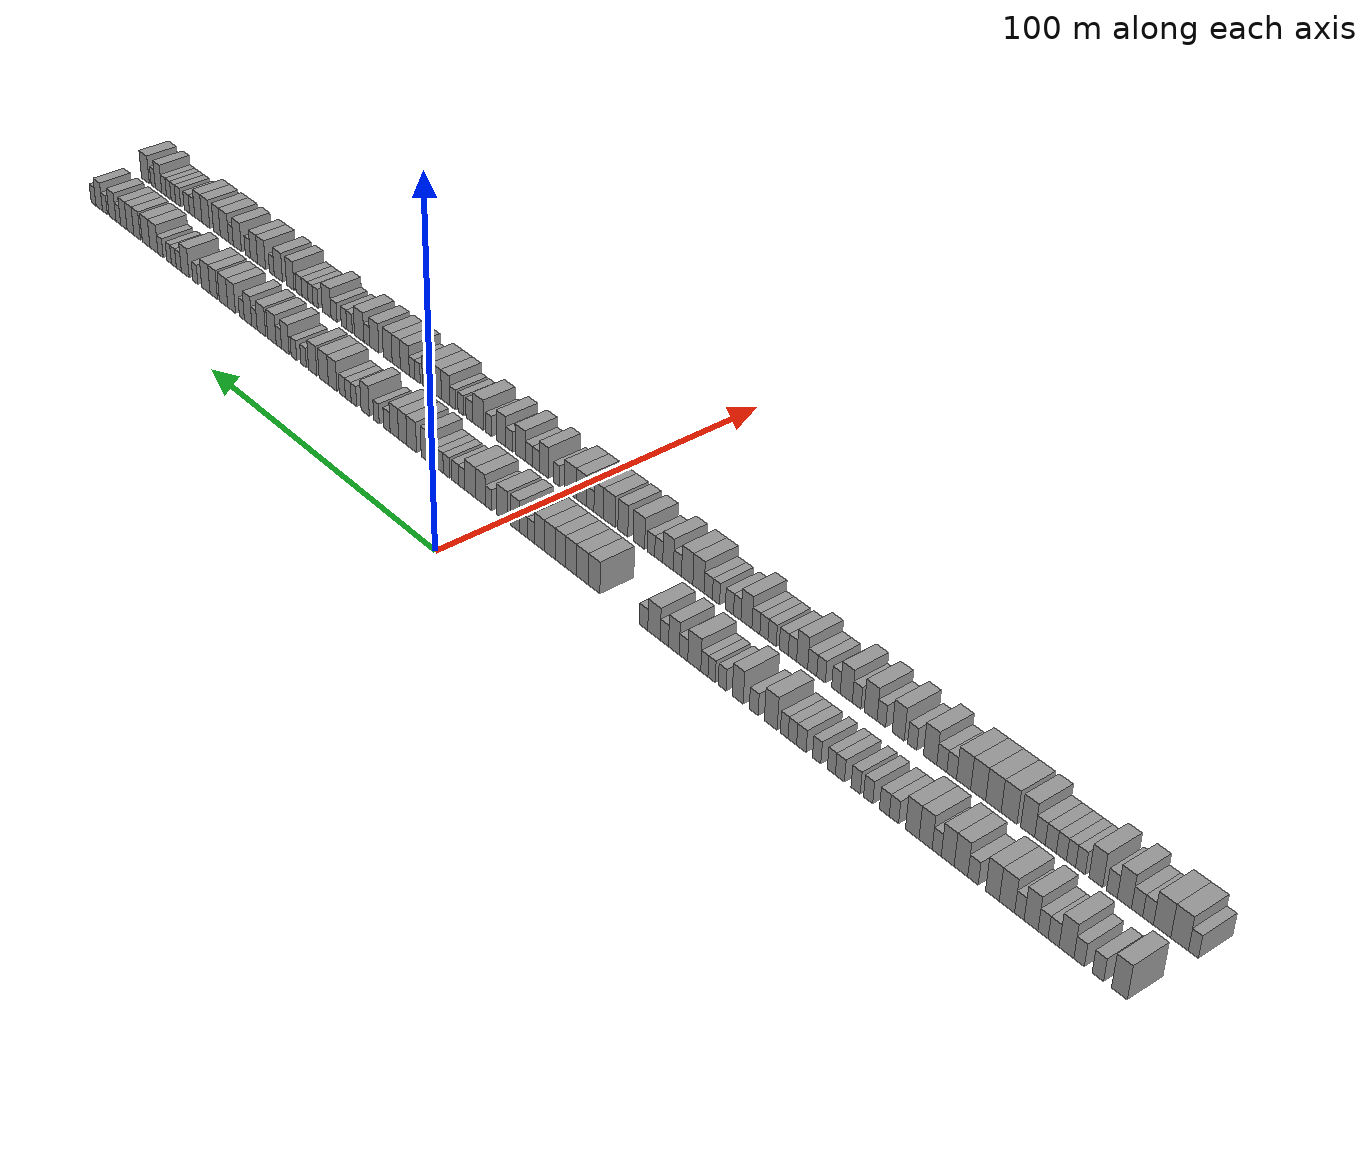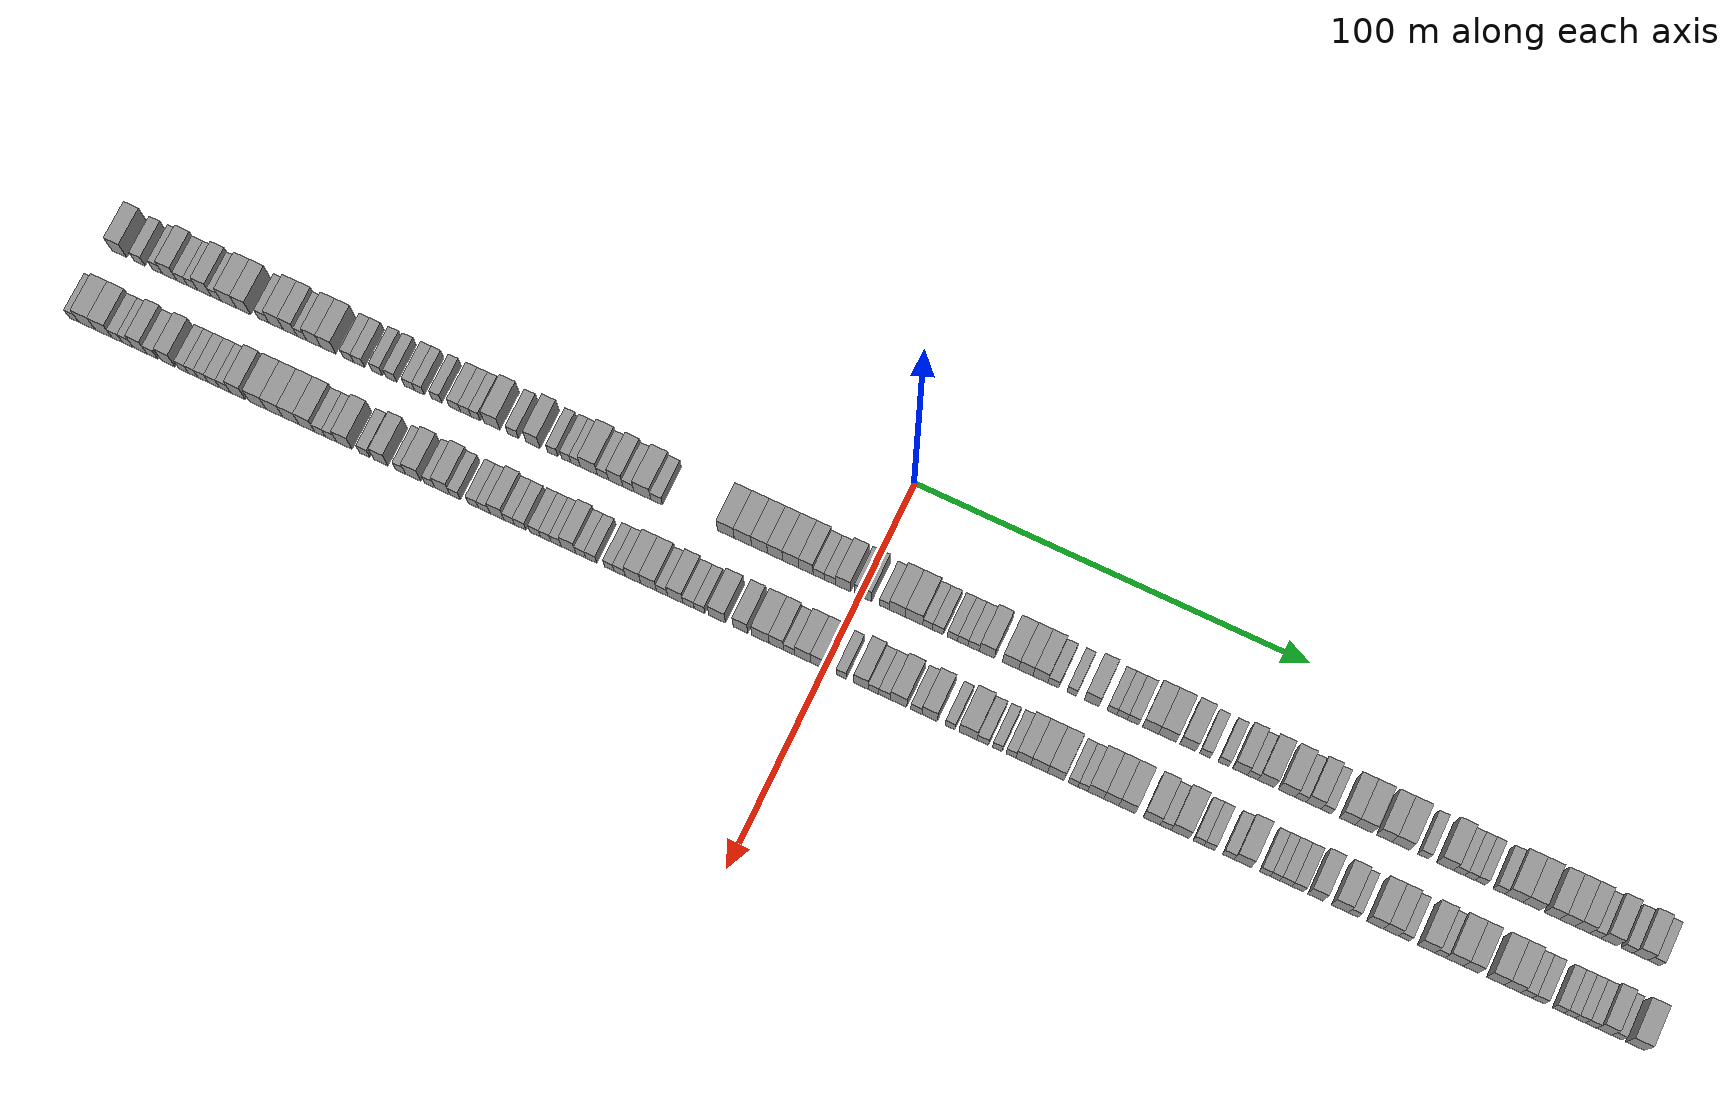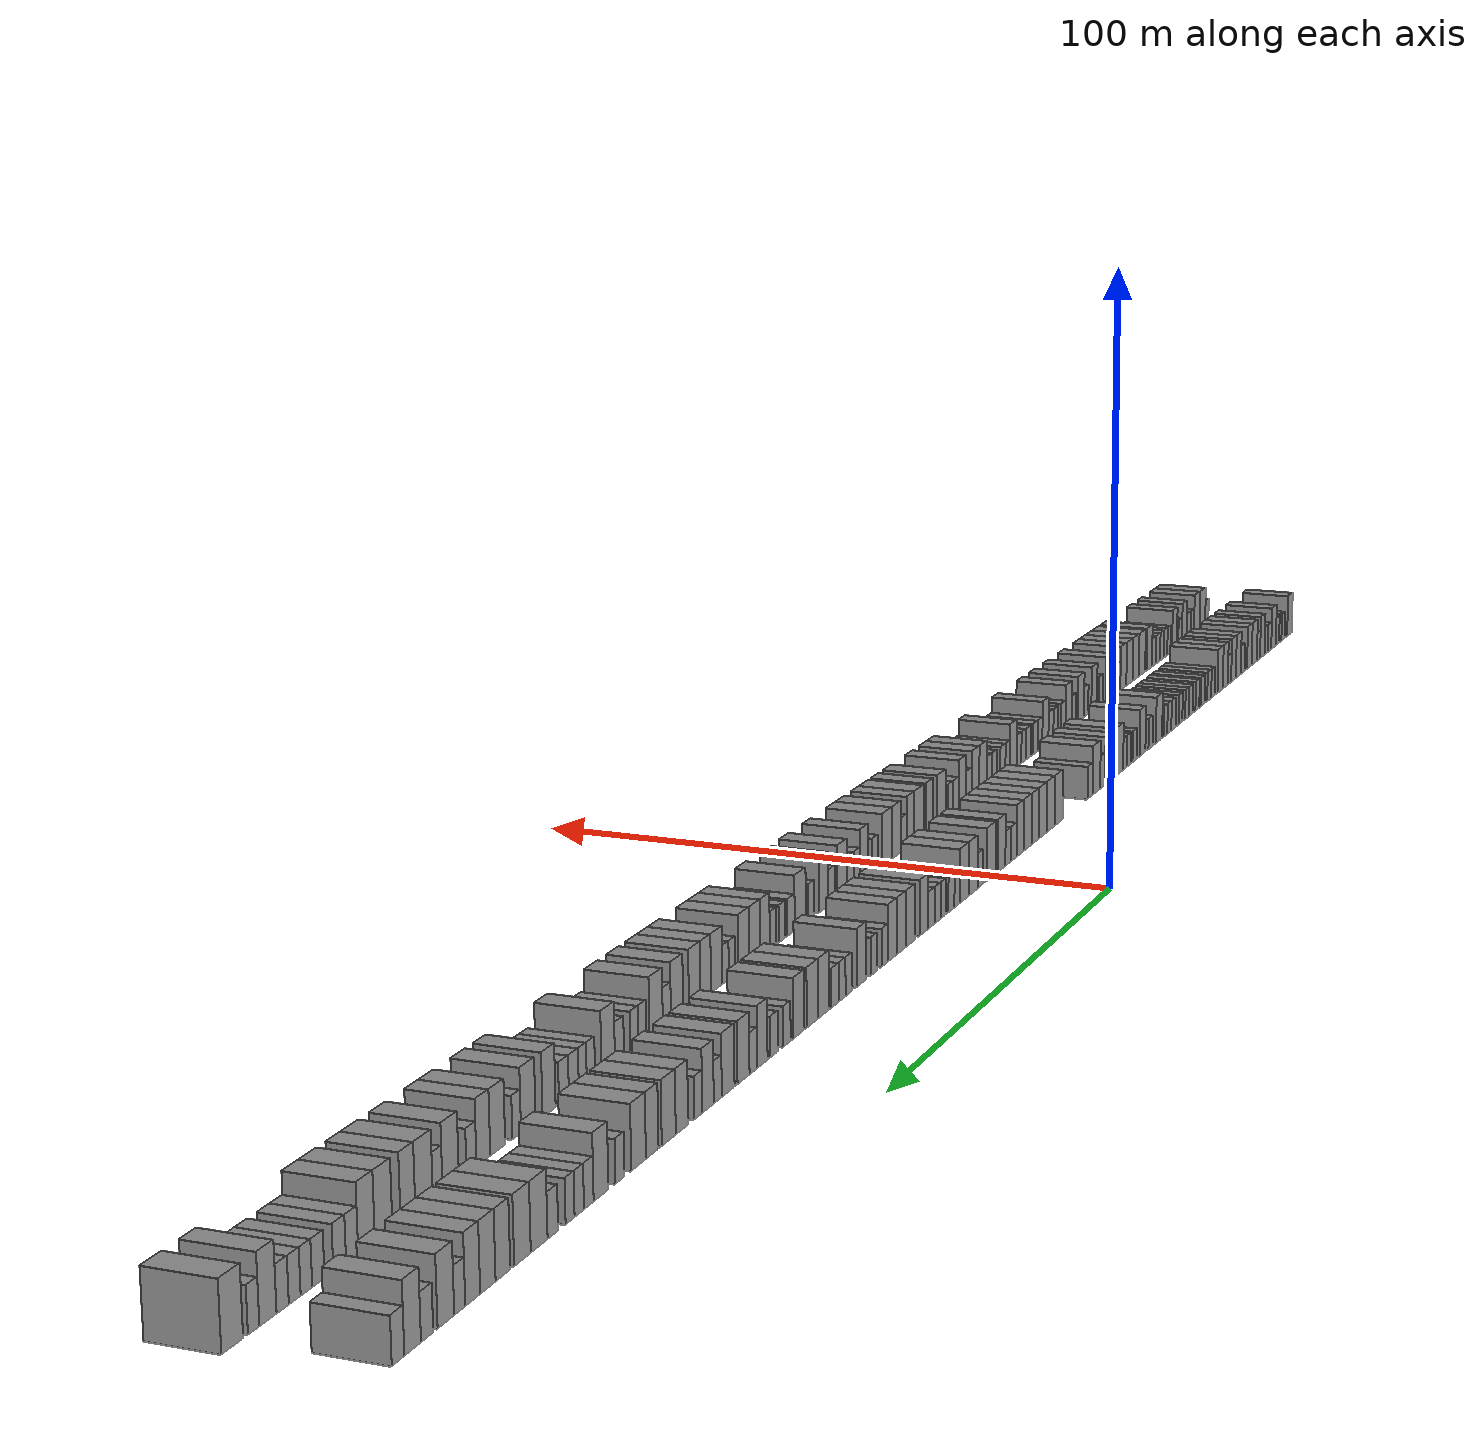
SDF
<sdf version="1.6">
 <world name="default">
  <scene>
   <sky><clouds><speed>12</speed></clouds></sky>
   <ambient>0.4 0.4 0.4 1</ambient>
   <background>0.7 0.7 0.7 1</background>
   <shadows>1</shadows>
  </scene>
  <gravity>0 0 -9.8066</gravity>
  <magnetic_field>6e-06 2.3e-05 -4.2e-05</magnetic_field>
  <physics default="0" name="default_physics" type="ode">
   <ode>
    <solver>
     <type>quick</type>
     <iters>10</iters>
     <sor>1.0</sor>
     <use_dynamic_moi_rescaling>0</use_dynamic_moi_rescaling>
    </solver>
    <constraints>
     <cfm>0</cfm>
     <erp>0.2</erp>
     <contact_max_correcting_vel>100</contact_max_correcting_vel>
     <contact_surface_layer>0.001</contact_surface_layer>
    </constraints>
   </ode>
   <max_step_size>0.004</max_step_size>
   <real_time_factor>1</real_time_factor>
   <real_time_update_rate>250</real_time_update_rate>
  </physics>
  <light name="sun" type="directional">
   <pose>0 0 10 0 0 0</pose>
   <diffuse>0.8 0.8 0.8 1</diffuse>
   <specular>0.2 0.2 0.2 1</specular>
   <attenuation>
    <range>1000</range>
    <constant>0.9</constant>
    <linear>0.01</linear>
    <quadratic>0.001</quadratic>
   </attenuation>
   <direction>-0.5 0.1 -0.9</direction>
  </light>
  <model name="building_1">
   <static>1</static>
   <pose>25.0000 -194.0165 0 0.000000 0.000000 0.000000</pose>
   <link name="link">
    <pose>0 0 4.50 0 0 0</pose>
    <collision name="collision"><geometry><box><size>10.0000 3.9670 9.0000</size></box></geometry></collision>
    <visual name="visual">
     <cast_shadows>0</cast_shadows>
     <geometry><box><size>10.0000 3.9670 9.0000</size></box></geometry>
     <material>
      <script>
       <uri>model://grey_wall/materials/scripts</uri>
       <uri>model://grey_wall/materials/textures</uri>
       <name>vrc/grey_wall</name>
      </script>
     </material>
    </visual>
   </link>
  </model>
  <model name="building_2">
   <static>1</static>
   <pose>25.0000 -188.5718 0 0.000000 0.000000 0.000000</pose>
   <link name="link">
    <pose>0 0 3.00 0 0 0</pose>
    <collision name="collision"><geometry><box><size>10.0000 2.9225 6.0000</size></box></geometry></collision>
    <visual name="visual">
     <cast_shadows>0</cast_shadows>
     <geometry><box><size>10.0000 2.9225 6.0000</size></box></geometry>
     <material>
      <script>
       <uri>model://grey_wall/materials/scripts</uri>
       <uri>model://grey_wall/materials/textures</uri>
       <name>vrc/grey_wall</name>
      </script>
     </material>
    </visual>
   </link>
  </model>
  <model name="building_3">
   <static>1</static>
   <pose>25.0000 -183.7584 0 0.000000 0.000000 0.000000</pose>
   <link name="link">
    <pose>0 0 3.00 0 0 0</pose>
    <collision name="collision"><geometry><box><size>10.0000 2.7043 6.0000</size></box></geometry></collision>
    <visual name="visual">
     <cast_shadows>0</cast_shadows>
     <geometry><box><size>10.0000 2.7043 6.0000</size></box></geometry>
     <material>
      <script>
       <uri>model://grey_wall/materials/scripts</uri>
       <uri>model://grey_wall/materials/textures</uri>
       <name>vrc/grey_wall</name>
      </script>
     </material>
    </visual>
   </link>
  </model>
  <model name="building_4">
   <static>1</static>
   <pose>25.0000 -180.4802 0 0.000000 0.000000 0.000000</pose>
   <link name="link">
    <pose>0 0 4.50 0 0 0</pose>
    <collision name="collision"><geometry><box><size>10.0000 3.8520 9.0000</size></box></geometry></collision>
    <visual name="visual">
     <cast_shadows>0</cast_shadows>
     <geometry><box><size>10.0000 3.8520 9.0000</size></box></geometry>
     <material>
      <script>
       <uri>model://grey_wall/materials/scripts</uri>
       <uri>model://grey_wall/materials/textures</uri>
       <name>vrc/grey_wall</name>
      </script>
     </material>
    </visual>
   </link>
  </model>
  <model name="building_5">
   <static>1</static>
   <pose>25.0000 -177.1076 0 0.000000 0.000000 0.000000</pose>
   <link name="link">
    <pose>0 0 3.00 0 0 0</pose>
    <collision name="collision"><geometry><box><size>10.0000 2.8932 6.0000</size></box></geometry></collision>
    <visual name="visual">
     <cast_shadows>0</cast_shadows>
     <geometry><box><size>10.0000 2.8932 6.0000</size></box></geometry>
     <material>
      <script>
       <uri>model://grey_wall/materials/scripts</uri>
       <uri>model://grey_wall/materials/textures</uri>
       <name>vrc/grey_wall</name>
      </script>
     </material>
    </visual>
   </link>
  </model>
  <model name="building_6">
   <static>1</static>
   <pose>25.0000 -174.3342 0 0.000000 0.000000 0.000000</pose>
   <link name="link">
    <pose>0 0 3.00 0 0 0</pose>
    <collision name="collision"><geometry><box><size>10.0000 2.6536 6.0000</size></box></geometry></collision>
    <visual name="visual">
     <cast_shadows>0</cast_shadows>
     <geometry><box><size>10.0000 2.6536 6.0000</size></box></geometry>
     <material>
      <script>
       <uri>model://grey_wall/materials/scripts</uri>
       <uri>model://grey_wall/materials/textures</uri>
       <name>vrc/grey_wall</name>
      </script>
     </material>
    </visual>
   </link>
  </model>
  <model name="building_7">
   <static>1</static>
   <pose>25.0000 -171.1680 0 0.000000 0.000000 0.000000</pose>
   <link name="link">
    <pose>0 0 4.50 0 0 0</pose>
    <collision name="collision"><geometry><box><size>10.0000 3.6788 9.0000</size></box></geometry></collision>
    <visual name="visual">
     <cast_shadows>0</cast_shadows>
     <geometry><box><size>10.0000 3.6788 9.0000</size></box></geometry>
     <material>
      <script>
       <uri>model://grey_wall/materials/scripts</uri>
       <uri>model://grey_wall/materials/textures</uri>
       <name>vrc/grey_wall</name>
      </script>
     </material>
    </visual>
   </link>
  </model>
  <model name="building_8">
   <static>1</static>
   <pose>25.0000 -168.0481 0 0.000000 0.000000 0.000000</pose>
   <link name="link">
    <pose>0 0 3.00 0 0 0</pose>
    <collision name="collision"><geometry><box><size>10.0000 2.5609 6.0000</size></box></geometry></collision>
    <visual name="visual">
     <cast_shadows>0</cast_shadows>
     <geometry><box><size>10.0000 2.5609 6.0000</size></box></geometry>
     <material>
      <script>
       <uri>model://grey_wall/materials/scripts</uri>
       <uri>model://grey_wall/materials/textures</uri>
       <name>vrc/grey_wall</name>
      </script>
     </material>
    </visual>
   </link>
  </model>
  <model name="building_9">
   <static>1</static>
   <pose>25.0000 -164.6973 0 0.000000 0.000000 0.000000</pose>
   <link name="link">
    <pose>0 0 4.50 0 0 0</pose>
    <collision name="collision"><geometry><box><size>10.0000 4.1407 9.0000</size></box></geometry></collision>
    <visual name="visual">
     <cast_shadows>0</cast_shadows>
     <geometry><box><size>10.0000 4.1407 9.0000</size></box></geometry>
     <material>
      <script>
       <uri>model://grey_wall/materials/scripts</uri>
       <uri>model://grey_wall/materials/textures</uri>
       <name>vrc/grey_wall</name>
      </script>
     </material>
    </visual>
   </link>
  </model>
  <model name="building_10">
   <static>1</static>
   <pose>25.0000 -160.7534 0 0.000000 0.000000 0.000000</pose>
   <link name="link">
    <pose>0 0 4.50 0 0 0</pose>
    <collision name="collision"><geometry><box><size>10.0000 3.7471 9.0000</size></box></geometry></collision>
    <visual name="visual">
     <cast_shadows>0</cast_shadows>
     <geometry><box><size>10.0000 3.7471 9.0000</size></box></geometry>
     <material>
      <script>
       <uri>model://grey_wall/materials/scripts</uri>
       <uri>model://grey_wall/materials/textures</uri>
       <name>vrc/grey_wall</name>
      </script>
     </material>
    </visual>
   </link>
  </model>
  <model name="building_11">
   <static>1</static>
   <pose>25.0000 -155.4140 0 0.000000 0.000000 0.000000</pose>
   <link name="link">
    <pose>0 0 3.00 0 0 0</pose>
    <collision name="collision"><geometry><box><size>10.0000 2.9317 6.0000</size></box></geometry></collision>
    <visual name="visual">
     <cast_shadows>0</cast_shadows>
     <geometry><box><size>10.0000 2.9317 6.0000</size></box></geometry>
     <material>
      <script>
       <uri>model://grey_wall/materials/scripts</uri>
       <uri>model://grey_wall/materials/textures</uri>
       <name>vrc/grey_wall</name>
      </script>
     </material>
    </visual>
   </link>
  </model>
  <model name="building_12">
   <static>1</static>
   <pose>25.0000 -152.0537 0 0.000000 0.000000 0.000000</pose>
   <link name="link">
    <pose>0 0 4.50 0 0 0</pose>
    <collision name="collision"><geometry><box><size>10.0000 3.7888 9.0000</size></box></geometry></collision>
    <visual name="visual">
     <cast_shadows>0</cast_shadows>
     <geometry><box><size>10.0000 3.7888 9.0000</size></box></geometry>
     <material>
      <script>
       <uri>model://grey_wall/materials/scripts</uri>
       <uri>model://grey_wall/materials/textures</uri>
       <name>vrc/grey_wall</name>
      </script>
     </material>
    </visual>
   </link>
  </model>
  <model name="building_13">
   <static>1</static>
   <pose>25.0000 -148.3409 0 0.000000 0.000000 0.000000</pose>
   <link name="link">
    <pose>0 0 4.50 0 0 0</pose>
    <collision name="collision"><geometry><box><size>10.0000 3.6369 9.0000</size></box></geometry></collision>
    <visual name="visual">
     <cast_shadows>0</cast_shadows>
     <geometry><box><size>10.0000 3.6369 9.0000</size></box></geometry>
     <material>
      <script>
       <uri>model://grey_wall/materials/scripts</uri>
       <uri>model://grey_wall/materials/textures</uri>
       <name>vrc/grey_wall</name>
      </script>
     </material>
    </visual>
   </link>
  </model>
  <model name="building_14">
   <static>1</static>
   <pose>25.0000 -145.2305 0 0.000000 0.000000 0.000000</pose>
   <link name="link">
    <pose>0 0 3.00 0 0 0</pose>
    <collision name="collision"><geometry><box><size>10.0000 2.5838 6.0000</size></box></geometry></collision>
    <visual name="visual">
     <cast_shadows>0</cast_shadows>
     <geometry><box><size>10.0000 2.5838 6.0000</size></box></geometry>
     <material>
      <script>
       <uri>model://grey_wall/materials/scripts</uri>
       <uri>model://grey_wall/materials/textures</uri>
       <name>vrc/grey_wall</name>
      </script>
     </material>
    </visual>
   </link>
  </model>
  <model name="building_15">
   <static>1</static>
   <pose>25.0000 -142.0524 0 0.000000 0.000000 0.000000</pose>
   <link name="link">
    <pose>0 0 4.50 0 0 0</pose>
    <collision name="collision"><geometry><box><size>10.0000 3.7724 9.0000</size></box></geometry></collision>
    <visual name="visual">
     <cast_shadows>0</cast_shadows>
     <geometry><box><size>10.0000 3.7724 9.0000</size></box></geometry>
     <material>
      <script>
       <uri>model://grey_wall/materials/scripts</uri>
       <uri>model://grey_wall/materials/textures</uri>
       <name>vrc/grey_wall</name>
      </script>
     </material>
    </visual>
   </link>
  </model>
  <model name="building_16">
   <static>1</static>
   <pose>25.0000 -138.2094 0 0.000000 0.000000 0.000000</pose>
   <link name="link">
    <pose>0 0 4.50 0 0 0</pose>
    <collision name="collision"><geometry><box><size>10.0000 3.9137 9.0000</size></box></geometry></collision>
    <visual name="visual">
     <cast_shadows>0</cast_shadows>
     <geometry><box><size>10.0000 3.9137 9.0000</size></box></geometry>
     <material>
      <script>
       <uri>model://grey_wall/materials/scripts</uri>
       <uri>model://grey_wall/materials/textures</uri>
       <name>vrc/grey_wall</name>
      </script>
     </material>
    </visual>
   </link>
  </model>
  <model name="building_17">
   <static>1</static>
   <pose>25.0000 -132.8847 0 0.000000 0.000000 0.000000</pose>
   <link name="link">
    <pose>0 0 3.00 0 0 0</pose>
    <collision name="collision"><geometry><box><size>10.0000 2.7356 6.0000</size></box></geometry></collision>
    <visual name="visual">
     <cast_shadows>0</cast_shadows>
     <geometry><box><size>10.0000 2.7356 6.0000</size></box></geometry>
     <material>
      <script>
       <uri>model://grey_wall/materials/scripts</uri>
       <uri>model://grey_wall/materials/textures</uri>
       <name>vrc/grey_wall</name>
      </script>
     </material>
    </visual>
   </link>
  </model>
  <model name="building_18">
   <static>1</static>
   <pose>25.0000 -130.0702 0 0.000000 0.000000 0.000000</pose>
   <link name="link">
    <pose>0 0 3.00 0 0 0</pose>
    <collision name="collision"><geometry><box><size>10.0000 2.8935 6.0000</size></box></geometry></collision>
    <visual name="visual">
     <cast_shadows>0</cast_shadows>
     <geometry><box><size>10.0000 2.8935 6.0000</size></box></geometry>
     <material>
      <script>
       <uri>model://grey_wall/materials/scripts</uri>
       <uri>model://grey_wall/materials/textures</uri>
       <name>vrc/grey_wall</name>
      </script>
     </material>
    </visual>
   </link>
  </model>
  <model name="building_19">
   <static>1</static>
   <pose>25.0000 -125.2565 0 0.000000 0.000000 0.000000</pose>
   <link name="link">
    <pose>0 0 3.00 0 0 0</pose>
    <collision name="collision"><geometry><box><size>10.0000 2.7338 6.0000</size></box></geometry></collision>
    <visual name="visual">
     <cast_shadows>0</cast_shadows>
     <geometry><box><size>10.0000 2.7338 6.0000</size></box></geometry>
     <material>
      <script>
       <uri>model://grey_wall/materials/scripts</uri>
       <uri>model://grey_wall/materials/textures</uri>
       <name>vrc/grey_wall</name>
      </script>
     </material>
    </visual>
   </link>
  </model>
  <model name="building_20">
   <static>1</static>
   <pose>25.0000 -121.5013 0 0.000000 0.000000 0.000000</pose>
   <link name="link">
    <pose>0 0 3.00 0 0 0</pose>
    <collision name="collision"><geometry><box><size>10.0000 2.7766 6.0000</size></box></geometry></collision>
    <visual name="visual">
     <cast_shadows>0</cast_shadows>
     <geometry><box><size>10.0000 2.7766 6.0000</size></box></geometry>
     <material>
      <script>
       <uri>model://grey_wall/materials/scripts</uri>
       <uri>model://grey_wall/materials/textures</uri>
       <name>vrc/grey_wall</name>
      </script>
     </material>
    </visual>
   </link>
  </model>
  <model name="building_21">
   <static>1</static>
   <pose>25.0000 -116.7300 0 0.000000 0.000000 0.000000</pose>
   <link name="link">
    <pose>0 0 3.00 0 0 0</pose>
    <collision name="collision"><geometry><box><size>10.0000 2.7659 6.0000</size></box></geometry></collision>
    <visual name="visual">
     <cast_shadows>0</cast_shadows>
     <geometry><box><size>10.0000 2.7659 6.0000</size></box></geometry>
     <material>
      <script>
       <uri>model://grey_wall/materials/scripts</uri>
       <uri>model://grey_wall/materials/textures</uri>
       <name>vrc/grey_wall</name>
      </script>
     </material>
    </visual>
   </link>
  </model>
  <model name="building_22">
   <static>1</static>
   <pose>25.0000 -114.1130 0 0.000000 0.000000 0.000000</pose>
   <link name="link">
    <pose>0 0 3.00 0 0 0</pose>
    <collision name="collision"><geometry><box><size>10.0000 2.4680 6.0000</size></box></geometry></collision>
    <visual name="visual">
     <cast_shadows>0</cast_shadows>
     <geometry><box><size>10.0000 2.4680 6.0000</size></box></geometry>
     <material>
      <script>
       <uri>model://grey_wall/materials/scripts</uri>
       <uri>model://grey_wall/materials/textures</uri>
       <name>vrc/grey_wall</name>
      </script>
     </material>
    </visual>
   </link>
  </model>
  <model name="building_23">
   <static>1</static>
   <pose>25.0000 -109.5772 0 0.000000 0.000000 0.000000</pose>
   <link name="link">
    <pose>0 0 3.00 0 0 0</pose>
    <collision name="collision"><geometry><box><size>10.0000 2.6037 6.0000</size></box></geometry></collision>
    <visual name="visual">
     <cast_shadows>0</cast_shadows>
     <geometry><box><size>10.0000 2.6037 6.0000</size></box></geometry>
     <material>
      <script>
       <uri>model://grey_wall/materials/scripts</uri>
       <uri>model://grey_wall/materials/textures</uri>
       <name>vrc/grey_wall</name>
      </script>
     </material>
    </visual>
   </link>
  </model>
  <model name="building_24">
   <static>1</static>
   <pose>25.0000 -104.7983 0 0.000000 0.000000 0.000000</pose>
   <link name="link">
    <pose>0 0 3.00 0 0 0</pose>
    <collision name="collision"><geometry><box><size>10.0000 2.9540 6.0000</size></box></geometry></collision>
    <visual name="visual">
     <cast_shadows>0</cast_shadows>
     <geometry><box><size>10.0000 2.9540 6.0000</size></box></geometry>
     <material>
      <script>
       <uri>model://grey_wall/materials/scripts</uri>
       <uri>model://grey_wall/materials/textures</uri>
       <name>vrc/grey_wall</name>
      </script>
     </material>
    </visual>
   </link>
  </model>
  <model name="building_25">
   <static>1</static>
   <pose>25.0000 -101.9632 0 0.000000 0.000000 0.000000</pose>
   <link name="link">
    <pose>0 0 3.00 0 0 0</pose>
    <collision name="collision"><geometry><box><size>10.0000 2.7163 6.0000</size></box></geometry></collision>
    <visual name="visual">
     <cast_shadows>0</cast_shadows>
     <geometry><box><size>10.0000 2.7163 6.0000</size></box></geometry>
     <material>
      <script>
       <uri>model://grey_wall/materials/scripts</uri>
       <uri>model://grey_wall/materials/textures</uri>
       <name>vrc/grey_wall</name>
      </script>
     </material>
    </visual>
   </link>
  </model>
  <model name="building_26">
   <static>1</static>
   <pose>25.0000 -99.3712 0 0.000000 0.000000 0.000000</pose>
   <link name="link">
    <pose>0 0 3.00 0 0 0</pose>
    <collision name="collision"><geometry><box><size>10.0000 2.4677 6.0000</size></box></geometry></collision>
    <visual name="visual">
     <cast_shadows>0</cast_shadows>
     <geometry><box><size>10.0000 2.4677 6.0000</size></box></geometry>
     <material>
      <script>
       <uri>model://grey_wall/materials/scripts</uri>
       <uri>model://grey_wall/materials/textures</uri>
       <name>vrc/grey_wall</name>
      </script>
     </material>
    </visual>
   </link>
  </model>
  <model name="building_27">
   <static>1</static>
   <pose>25.0000 -95.0721 0 0.000000 0.000000 0.000000</pose>
   <link name="link">
    <pose>0 0 4.50 0 0 0</pose>
    <collision name="collision"><geometry><box><size>10.0000 4.1305 9.0000</size></box></geometry></collision>
    <visual name="visual">
     <cast_shadows>0</cast_shadows>
     <geometry><box><size>10.0000 4.1305 9.0000</size></box></geometry>
     <material>
      <script>
       <uri>model://grey_wall/materials/scripts</uri>
       <uri>model://grey_wall/materials/textures</uri>
       <name>vrc/grey_wall</name>
      </script>
     </material>
    </visual>
   </link>
  </model>
  <model name="building_28">
   <static>1</static>
   <pose>25.0000 -89.5736 0 0.000000 0.000000 0.000000</pose>
   <link name="link">
    <pose>0 0 3.00 0 0 0</pose>
    <collision name="collision"><geometry><box><size>10.0000 2.8665 6.0000</size></box></geometry></collision>
    <visual name="visual">
     <cast_shadows>0</cast_shadows>
     <geometry><box><size>10.0000 2.8665 6.0000</size></box></geometry>
     <material>
      <script>
       <uri>model://grey_wall/materials/scripts</uri>
       <uri>model://grey_wall/materials/textures</uri>
       <name>vrc/grey_wall</name>
      </script>
     </material>
    </visual>
   </link>
  </model>
  <model name="building_29">
   <static>1</static>
   <pose>25.0000 -84.3223 0 0.000000 0.000000 0.000000</pose>
   <link name="link">
    <pose>0 0 4.50 0 0 0</pose>
    <collision name="collision"><geometry><box><size>10.0000 3.6360 9.0000</size></box></geometry></collision>
    <visual name="visual">
     <cast_shadows>0</cast_shadows>
     <geometry><box><size>10.0000 3.6360 9.0000</size></box></geometry>
     <material>
      <script>
       <uri>model://grey_wall/materials/scripts</uri>
       <uri>model://grey_wall/materials/textures</uri>
       <name>vrc/grey_wall</name>
      </script>
     </material>
    </visual>
   </link>
  </model>
  <model name="building_30">
   <static>1</static>
   <pose>25.0000 -79.1929 0 0.000000 0.000000 0.000000</pose>
   <link name="link">
    <pose>0 0 3.00 0 0 0</pose>
    <collision name="collision"><geometry><box><size>10.0000 2.6228 6.0000</size></box></geometry></collision>
    <visual name="visual">
     <cast_shadows>0</cast_shadows>
     <geometry><box><size>10.0000 2.6228 6.0000</size></box></geometry>
     <material>
      <script>
       <uri>model://grey_wall/materials/scripts</uri>
       <uri>model://grey_wall/materials/textures</uri>
       <name>vrc/grey_wall</name>
      </script>
     </material>
    </visual>
   </link>
  </model>
  <model name="building_31">
   <static>1</static>
   <pose>25.0000 -75.6652 0 0.000000 0.000000 0.000000</pose>
   <link name="link">
    <pose>0 0 3.00 0 0 0</pose>
    <collision name="collision"><geometry><box><size>10.0000 2.4328 6.0000</size></box></geometry></collision>
    <visual name="visual">
     <cast_shadows>0</cast_shadows>
     <geometry><box><size>10.0000 2.4328 6.0000</size></box></geometry>
     <material>
      <script>
       <uri>model://grey_wall/materials/scripts</uri>
       <uri>model://grey_wall/materials/textures</uri>
       <name>vrc/grey_wall</name>
      </script>
     </material>
    </visual>
   </link>
  </model>
  <model name="building_32">
   <static>1</static>
   <pose>25.0000 -73.2357 0 0.000000 0.000000 0.000000</pose>
   <link name="link">
    <pose>0 0 3.00 0 0 0</pose>
    <collision name="collision"><geometry><box><size>10.0000 2.4261 6.0000</size></box></geometry></collision>
    <visual name="visual">
     <cast_shadows>0</cast_shadows>
     <geometry><box><size>10.0000 2.4261 6.0000</size></box></geometry>
     <material>
      <script>
       <uri>model://grey_wall/materials/scripts</uri>
       <uri>model://grey_wall/materials/textures</uri>
       <name>vrc/grey_wall</name>
      </script>
     </material>
    </visual>
   </link>
  </model>
  <model name="building_33">
   <static>1</static>
   <pose>25.0000 -69.8034 0 0.000000 0.000000 0.000000</pose>
   <link name="link">
    <pose>0 0 4.50 0 0 0</pose>
    <collision name="collision"><geometry><box><size>10.0000 4.4385 9.0000</size></box></geometry></collision>
    <visual name="visual">
     <cast_shadows>0</cast_shadows>
     <geometry><box><size>10.0000 4.4385 9.0000</size></box></geometry>
     <material>
      <script>
       <uri>model://grey_wall/materials/scripts</uri>
       <uri>model://grey_wall/materials/textures</uri>
       <name>vrc/grey_wall</name>
      </script>
     </material>
    </visual>
   </link>
  </model>
  <model name="building_34">
   <static>1</static>
   <pose>25.0000 -66.1217 0 0.000000 0.000000 0.000000</pose>
   <link name="link">
    <pose>0 0 3.00 0 0 0</pose>
    <collision name="collision"><geometry><box><size>10.0000 2.9249 6.0000</size></box></geometry></collision>
    <visual name="visual">
     <cast_shadows>0</cast_shadows>
     <geometry><box><size>10.0000 2.9249 6.0000</size></box></geometry>
     <material>
      <script>
       <uri>model://grey_wall/materials/scripts</uri>
       <uri>model://grey_wall/materials/textures</uri>
       <name>vrc/grey_wall</name>
      </script>
     </material>
    </visual>
   </link>
  </model>
  <model name="building_35">
   <static>1</static>
   <pose>25.0000 -62.8063 0 0.000000 0.000000 0.000000</pose>
   <link name="link">
    <pose>0 0 4.50 0 0 0</pose>
    <collision name="collision"><geometry><box><size>10.0000 3.7059 9.0000</size></box></geometry></collision>
    <visual name="visual">
     <cast_shadows>0</cast_shadows>
     <geometry><box><size>10.0000 3.7059 9.0000</size></box></geometry>
     <material>
      <script>
       <uri>model://grey_wall/materials/scripts</uri>
       <uri>model://grey_wall/materials/textures</uri>
       <name>vrc/grey_wall</name>
      </script>
     </material>
    </visual>
   </link>
  </model>
  <model name="building_36">
   <static>1</static>
   <pose>25.0000 -59.5107 0 0.000000 0.000000 0.000000</pose>
   <link name="link">
    <pose>0 0 3.00 0 0 0</pose>
    <collision name="collision"><geometry><box><size>10.0000 2.8853 6.0000</size></box></geometry></collision>
    <visual name="visual">
     <cast_shadows>0</cast_shadows>
     <geometry><box><size>10.0000 2.8853 6.0000</size></box></geometry>
     <material>
      <script>
       <uri>model://grey_wall/materials/scripts</uri>
       <uri>model://grey_wall/materials/textures</uri>
       <name>vrc/grey_wall</name>
      </script>
     </material>
    </visual>
   </link>
  </model>
  <model name="building_37">
   <static>1</static>
   <pose>25.0000 -55.8811 0 0.000000 0.000000 0.000000</pose>
   <link name="link">
    <pose>0 0 4.50 0 0 0</pose>
    <collision name="collision"><geometry><box><size>10.0000 4.3738 9.0000</size></box></geometry></collision>
    <visual name="visual">
     <cast_shadows>0</cast_shadows>
     <geometry><box><size>10.0000 4.3738 9.0000</size></box></geometry>
     <material>
      <script>
       <uri>model://grey_wall/materials/scripts</uri>
       <uri>model://grey_wall/materials/textures</uri>
       <name>vrc/grey_wall</name>
      </script>
     </material>
    </visual>
   </link>
  </model>
  <model name="building_38">
   <static>1</static>
   <pose>25.0000 -52.2122 0 0.000000 0.000000 0.000000</pose>
   <link name="link">
    <pose>0 0 3.00 0 0 0</pose>
    <collision name="collision"><geometry><box><size>10.0000 2.9640 6.0000</size></box></geometry></collision>
    <visual name="visual">
     <cast_shadows>0</cast_shadows>
     <geometry><box><size>10.0000 2.9640 6.0000</size></box></geometry>
     <material>
      <script>
       <uri>model://grey_wall/materials/scripts</uri>
       <uri>model://grey_wall/materials/textures</uri>
       <name>vrc/grey_wall</name>
      </script>
     </material>
    </visual>
   </link>
  </model>
  <model name="building_39">
   <static>1</static>
   <pose>25.0000 -34.3294 0 0.000000 0.000000 0.000000</pose>
   <link name="link">
    <pose>0 0 4.50 0 0 0</pose>
    <collision name="collision"><geometry><box><size>10.0000 4.2672 9.0000</size></box></geometry></collision>
    <visual name="visual">
     <cast_shadows>0</cast_shadows>
     <geometry><box><size>10.0000 4.2672 9.0000</size></box></geometry>
     <material>
      <script>
       <uri>model://grey_wall/materials/scripts</uri>
       <uri>model://grey_wall/materials/textures</uri>
       <name>vrc/grey_wall</name>
      </script>
     </material>
    </visual>
   </link>
  </model>
  <model name="building_40">
   <static>1</static>
   <pose>25.0000 -29.9537 0 0.000000 0.000000 0.000000</pose>
   <link name="link">
    <pose>0 0 4.50 0 0 0</pose>
    <collision name="collision"><geometry><box><size>10.0000 4.4841 9.0000</size></box></geometry></collision>
    <visual name="visual">
     <cast_shadows>0</cast_shadows>
     <geometry><box><size>10.0000 4.4841 9.0000</size></box></geometry>
     <material>
      <script>
       <uri>model://grey_wall/materials/scripts</uri>
       <uri>model://grey_wall/materials/textures</uri>
       <name>vrc/grey_wall</name>
      </script>
     </material>
    </visual>
   </link>
  </model>
  <model name="building_41">
   <static>1</static>
   <pose>25.0000 -25.6573 0 0.000000 0.000000 0.000000</pose>
   <link name="link">
    <pose>0 0 4.50 0 0 0</pose>
    <collision name="collision"><geometry><box><size>10.0000 4.1088 9.0000</size></box></geometry></collision>
    <visual name="visual">
     <cast_shadows>0</cast_shadows>
     <geometry><box><size>10.0000 4.1088 9.0000</size></box></geometry>
     <material>
      <script>
       <uri>model://grey_wall/materials/scripts</uri>
       <uri>model://grey_wall/materials/textures</uri>
       <name>vrc/grey_wall</name>
      </script>
     </material>
    </visual>
   </link>
  </model>
  <model name="building_42">
   <static>1</static>
   <pose>25.0000 -21.6705 0 0.000000 0.000000 0.000000</pose>
   <link name="link">
    <pose>0 0 4.50 0 0 0</pose>
    <collision name="collision"><geometry><box><size>10.0000 3.8647 9.0000</size></box></geometry></collision>
    <visual name="visual">
     <cast_shadows>0</cast_shadows>
     <geometry><box><size>10.0000 3.8647 9.0000</size></box></geometry>
     <material>
      <script>
       <uri>model://grey_wall/materials/scripts</uri>
       <uri>model://grey_wall/materials/textures</uri>
       <name>vrc/grey_wall</name>
      </script>
     </material>
    </visual>
   </link>
  </model>
  <model name="building_43">
   <static>1</static>
   <pose>25.0000 -17.6612 0 0.000000 0.000000 0.000000</pose>
   <link name="link">
    <pose>0 0 4.50 0 0 0</pose>
    <collision name="collision"><geometry><box><size>10.0000 4.1541 9.0000</size></box></geometry></collision>
    <visual name="visual">
     <cast_shadows>0</cast_shadows>
     <geometry><box><size>10.0000 4.1541 9.0000</size></box></geometry>
     <material>
      <script>
       <uri>model://grey_wall/materials/scripts</uri>
       <uri>model://grey_wall/materials/textures</uri>
       <name>vrc/grey_wall</name>
      </script>
     </material>
    </visual>
   </link>
  </model>
  <model name="building_44">
   <static>1</static>
   <pose>25.0000 -13.7637 0 0.000000 0.000000 0.000000</pose>
   <link name="link">
    <pose>0 0 4.50 0 0 0</pose>
    <collision name="collision"><geometry><box><size>10.0000 3.6408 9.0000</size></box></geometry></collision>
    <visual name="visual">
     <cast_shadows>0</cast_shadows>
     <geometry><box><size>10.0000 3.6408 9.0000</size></box></geometry>
     <material>
      <script>
       <uri>model://grey_wall/materials/scripts</uri>
       <uri>model://grey_wall/materials/textures</uri>
       <name>vrc/grey_wall</name>
      </script>
     </material>
    </visual>
   </link>
  </model>
  <model name="building_45">
   <static>1</static>
   <pose>25.0000 -10.5252 0 0.000000 0.000000 0.000000</pose>
   <link name="link">
    <pose>0 0 3.00 0 0 0</pose>
    <collision name="collision"><geometry><box><size>10.0000 2.8363 6.0000</size></box></geometry></collision>
    <visual name="visual">
     <cast_shadows>0</cast_shadows>
     <geometry><box><size>10.0000 2.8363 6.0000</size></box></geometry>
     <material>
      <script>
       <uri>model://grey_wall/materials/scripts</uri>
       <uri>model://grey_wall/materials/textures</uri>
       <name>vrc/grey_wall</name>
      </script>
     </material>
    </visual>
   </link>
  </model>
  <model name="building_46">
   <static>1</static>
   <pose>25.0000 -7.6278 0 0.000000 0.000000 0.000000</pose>
   <link name="link">
    <pose>0 0 3.00 0 0 0</pose>
    <collision name="collision"><geometry><box><size>10.0000 2.9585 6.0000</size></box></geometry></collision>
    <visual name="visual">
     <cast_shadows>0</cast_shadows>
     <geometry><box><size>10.0000 2.9585 6.0000</size></box></geometry>
     <material>
      <script>
       <uri>model://grey_wall/materials/scripts</uri>
       <uri>model://grey_wall/materials/textures</uri>
       <name>vrc/grey_wall</name>
      </script>
     </material>
    </visual>
   </link>
  </model>
  <model name="building_47">
   <static>1</static>
   <pose>25.0000 -4.2563 0 0.000000 0.000000 0.000000</pose>
   <link name="link">
    <pose>0 0 4.50 0 0 0</pose>
    <collision name="collision"><geometry><box><size>10.0000 3.7844 9.0000</size></box></geometry></collision>
    <visual name="visual">
     <cast_shadows>0</cast_shadows>
     <geometry><box><size>10.0000 3.7844 9.0000</size></box></geometry>
     <material>
      <script>
       <uri>model://grey_wall/materials/scripts</uri>
       <uri>model://grey_wall/materials/textures</uri>
       <name>vrc/grey_wall</name>
      </script>
     </material>
    </visual>
   </link>
  </model>
  <model name="building_48">
   <static>1</static>
   <pose>25.0000 0.8295 0 0.000000 0.000000 0.000000</pose>
   <link name="link">
    <pose>0 0 4.50 0 0 0</pose>
    <collision name="collision"><geometry><box><size>10.0000 4.3873 9.0000</size></box></geometry></collision>
    <visual name="visual">
     <cast_shadows>0</cast_shadows>
     <geometry><box><size>10.0000 4.3873 9.0000</size></box></geometry>
     <material>
      <script>
       <uri>model://grey_wall/materials/scripts</uri>
       <uri>model://grey_wall/materials/textures</uri>
       <name>vrc/grey_wall</name>
      </script>
     </material>
    </visual>
   </link>
  </model>
  <model name="building_49">
   <static>1</static>
   <pose>25.0000 6.2965 0 0.000000 0.000000 0.000000</pose>
   <link name="link">
    <pose>0 0 3.00 0 0 0</pose>
    <collision name="collision"><geometry><box><size>10.0000 2.5467 6.0000</size></box></geometry></collision>
    <visual name="visual">
     <cast_shadows>0</cast_shadows>
     <geometry><box><size>10.0000 2.5467 6.0000</size></box></geometry>
     <material>
      <script>
       <uri>model://grey_wall/materials/scripts</uri>
       <uri>model://grey_wall/materials/textures</uri>
       <name>vrc/grey_wall</name>
      </script>
     </material>
    </visual>
   </link>
  </model>
  <model name="building_50">
   <static>1</static>
   <pose>25.0000 9.5672 0 0.000000 0.000000 0.000000</pose>
   <link name="link">
    <pose>0 0 4.50 0 0 0</pose>
    <collision name="collision"><geometry><box><size>10.0000 3.9947 9.0000</size></box></geometry></collision>
    <visual name="visual">
     <cast_shadows>0</cast_shadows>
     <geometry><box><size>10.0000 3.9947 9.0000</size></box></geometry>
     <material>
      <script>
       <uri>model://grey_wall/materials/scripts</uri>
       <uri>model://grey_wall/materials/textures</uri>
       <name>vrc/grey_wall</name>
      </script>
     </material>
    </visual>
   </link>
  </model>
  <model name="building_51">
   <static>1</static>
   <pose>25.0000 13.7951 0 0.000000 0.000000 0.000000</pose>
   <link name="link">
    <pose>0 0 4.50 0 0 0</pose>
    <collision name="collision"><geometry><box><size>10.0000 4.4612 9.0000</size></box></geometry></collision>
    <visual name="visual">
     <cast_shadows>0</cast_shadows>
     <geometry><box><size>10.0000 4.4612 9.0000</size></box></geometry>
     <material>
      <script>
       <uri>model://grey_wall/materials/scripts</uri>
       <uri>model://grey_wall/materials/textures</uri>
       <name>vrc/grey_wall</name>
      </script>
     </material>
    </visual>
   </link>
  </model>
  <model name="building_52">
   <static>1</static>
   <pose>25.0000 17.2621 0 0.000000 0.000000 0.000000</pose>
   <link name="link">
    <pose>0 0 3.00 0 0 0</pose>
    <collision name="collision"><geometry><box><size>10.0000 2.4728 6.0000</size></box></geometry></collision>
    <visual name="visual">
     <cast_shadows>0</cast_shadows>
     <geometry><box><size>10.0000 2.4728 6.0000</size></box></geometry>
     <material>
      <script>
       <uri>model://grey_wall/materials/scripts</uri>
       <uri>model://grey_wall/materials/textures</uri>
       <name>vrc/grey_wall</name>
      </script>
     </material>
    </visual>
   </link>
  </model>
  <model name="building_53">
   <static>1</static>
   <pose>25.0000 19.8947 0 0.000000 0.000000 0.000000</pose>
   <link name="link">
    <pose>0 0 3.00 0 0 0</pose>
    <collision name="collision"><geometry><box><size>10.0000 2.7923 6.0000</size></box></geometry></collision>
    <visual name="visual">
     <cast_shadows>0</cast_shadows>
     <geometry><box><size>10.0000 2.7923 6.0000</size></box></geometry>
     <material>
      <script>
       <uri>model://grey_wall/materials/scripts</uri>
       <uri>model://grey_wall/materials/textures</uri>
       <name>vrc/grey_wall</name>
      </script>
     </material>
    </visual>
   </link>
  </model>
  <model name="building_54">
   <static>1</static>
   <pose>25.0000 23.5818 0 0.000000 0.000000 0.000000</pose>
   <link name="link">
    <pose>0 0 3.00 0 0 0</pose>
    <collision name="collision"><geometry><box><size>10.0000 2.5820 6.0000</size></box></geometry></collision>
    <visual name="visual">
     <cast_shadows>0</cast_shadows>
     <geometry><box><size>10.0000 2.5820 6.0000</size></box></geometry>
     <material>
      <script>
       <uri>model://grey_wall/materials/scripts</uri>
       <uri>model://grey_wall/materials/textures</uri>
       <name>vrc/grey_wall</name>
      </script>
     </material>
    </visual>
   </link>
  </model>
  <model name="building_55">
   <static>1</static>
   <pose>25.0000 26.1782 0 0.000000 0.000000 0.000000</pose>
   <link name="link">
    <pose>0 0 3.00 0 0 0</pose>
    <collision name="collision"><geometry><box><size>10.0000 2.6108 6.0000</size></box></geometry></collision>
    <visual name="visual">
     <cast_shadows>0</cast_shadows>
     <geometry><box><size>10.0000 2.6108 6.0000</size></box></geometry>
     <material>
      <script>
       <uri>model://grey_wall/materials/scripts</uri>
       <uri>model://grey_wall/materials/textures</uri>
       <name>vrc/grey_wall</name>
      </script>
     </material>
    </visual>
   </link>
  </model>
  <model name="building_56">
   <static>1</static>
   <pose>25.0000 28.9518 0 0.000000 0.000000 0.000000</pose>
   <link name="link">
    <pose>0 0 3.00 0 0 0</pose>
    <collision name="collision"><geometry><box><size>10.0000 2.9364 6.0000</size></box></geometry></collision>
    <visual name="visual">
     <cast_shadows>0</cast_shadows>
     <geometry><box><size>10.0000 2.9364 6.0000</size></box></geometry>
     <material>
      <script>
       <uri>model://grey_wall/materials/scripts</uri>
       <uri>model://grey_wall/materials/textures</uri>
       <name>vrc/grey_wall</name>
      </script>
     </material>
    </visual>
   </link>
  </model>
  <model name="building_57">
   <static>1</static>
   <pose>25.0000 32.3154 0 0.000000 0.000000 0.000000</pose>
   <link name="link">
    <pose>0 0 4.50 0 0 0</pose>
    <collision name="collision"><geometry><box><size>10.0000 3.7908 9.0000</size></box></geometry></collision>
    <visual name="visual">
     <cast_shadows>0</cast_shadows>
     <geometry><box><size>10.0000 3.7908 9.0000</size></box></geometry>
     <material>
      <script>
       <uri>model://grey_wall/materials/scripts</uri>
       <uri>model://grey_wall/materials/textures</uri>
       <name>vrc/grey_wall</name>
      </script>
     </material>
    </visual>
   </link>
  </model>
  <model name="building_58">
   <static>1</static>
   <pose>25.0000 38.2663 0 0.000000 0.000000 0.000000</pose>
   <link name="link">
    <pose>0 0 4.50 0 0 0</pose>
    <collision name="collision"><geometry><box><size>10.0000 4.1110 9.0000</size></box></geometry></collision>
    <visual name="visual">
     <cast_shadows>0</cast_shadows>
     <geometry><box><size>10.0000 4.1110 9.0000</size></box></geometry>
     <material>
      <script>
       <uri>model://grey_wall/materials/scripts</uri>
       <uri>model://grey_wall/materials/textures</uri>
       <name>vrc/grey_wall</name>
      </script>
     </material>
    </visual>
   </link>
  </model>
  <model name="building_59">
   <static>1</static>
   <pose>25.0000 42.1359 0 0.000000 0.000000 0.000000</pose>
   <link name="link">
    <pose>0 0 4.50 0 0 0</pose>
    <collision name="collision"><geometry><box><size>10.0000 3.6283 9.0000</size></box></geometry></collision>
    <visual name="visual">
     <cast_shadows>0</cast_shadows>
     <geometry><box><size>10.0000 3.6283 9.0000</size></box></geometry>
     <material>
      <script>
       <uri>model://grey_wall/materials/scripts</uri>
       <uri>model://grey_wall/materials/textures</uri>
       <name>vrc/grey_wall</name>
      </script>
     </material>
    </visual>
   </link>
  </model>
  <model name="building_60">
   <static>1</static>
   <pose>25.0000 45.8025 0 0.000000 0.000000 0.000000</pose>
   <link name="link">
    <pose>0 0 4.50 0 0 0</pose>
    <collision name="collision"><geometry><box><size>10.0000 3.7048 9.0000</size></box></geometry></collision>
    <visual name="visual">
     <cast_shadows>0</cast_shadows>
     <geometry><box><size>10.0000 3.7048 9.0000</size></box></geometry>
     <material>
      <script>
       <uri>model://grey_wall/materials/scripts</uri>
       <uri>model://grey_wall/materials/textures</uri>
       <name>vrc/grey_wall</name>
      </script>
     </material>
    </visual>
   </link>
  </model>
  <model name="building_61">
   <static>1</static>
   <pose>25.0000 49.0504 0 0.000000 0.000000 0.000000</pose>
   <link name="link">
    <pose>0 0 3.00 0 0 0</pose>
    <collision name="collision"><geometry><box><size>10.0000 2.7910 6.0000</size></box></geometry></collision>
    <visual name="visual">
     <cast_shadows>0</cast_shadows>
     <geometry><box><size>10.0000 2.7910 6.0000</size></box></geometry>
     <material>
      <script>
       <uri>model://grey_wall/materials/scripts</uri>
       <uri>model://grey_wall/materials/textures</uri>
       <name>vrc/grey_wall</name>
      </script>
     </material>
    </visual>
   </link>
  </model>
  <model name="building_62">
   <static>1</static>
   <pose>25.0000 53.6523 0 0.000000 0.000000 0.000000</pose>
   <link name="link">
    <pose>0 0 3.00 0 0 0</pose>
    <collision name="collision"><geometry><box><size>10.0000 2.4130 6.0000</size></box></geometry></collision>
    <visual name="visual">
     <cast_shadows>0</cast_shadows>
     <geometry><box><size>10.0000 2.4130 6.0000</size></box></geometry>
     <material>
      <script>
       <uri>model://grey_wall/materials/scripts</uri>
       <uri>model://grey_wall/materials/textures</uri>
       <name>vrc/grey_wall</name>
      </script>
     </material>
    </visual>
   </link>
  </model>
  <model name="building_63">
   <static>1</static>
   <pose>25.0000 58.6993 0 0.000000 0.000000 0.000000</pose>
   <link name="link">
    <pose>0 0 4.50 0 0 0</pose>
    <collision name="collision"><geometry><box><size>10.0000 3.6810 9.0000</size></box></geometry></collision>
    <visual name="visual">
     <cast_shadows>0</cast_shadows>
     <geometry><box><size>10.0000 3.6810 9.0000</size></box></geometry>
     <material>
      <script>
       <uri>model://grey_wall/materials/scripts</uri>
       <uri>model://grey_wall/materials/textures</uri>
       <name>vrc/grey_wall</name>
      </script>
     </material>
    </visual>
   </link>
  </model>
  <model name="building_64">
   <static>1</static>
   <pose>25.0000 63.7646 0 0.000000 0.000000 0.000000</pose>
   <link name="link">
    <pose>0 0 3.00 0 0 0</pose>
    <collision name="collision"><geometry><box><size>10.0000 2.4495 6.0000</size></box></geometry></collision>
    <visual name="visual">
     <cast_shadows>0</cast_shadows>
     <geometry><box><size>10.0000 2.4495 6.0000</size></box></geometry>
     <material>
      <script>
       <uri>model://grey_wall/materials/scripts</uri>
       <uri>model://grey_wall/materials/textures</uri>
       <name>vrc/grey_wall</name>
      </script>
     </material>
    </visual>
   </link>
  </model>
  <model name="building_65">
   <static>1</static>
   <pose>25.0000 66.3241 0 0.000000 0.000000 0.000000</pose>
   <link name="link">
    <pose>0 0 3.00 0 0 0</pose>
    <collision name="collision"><geometry><box><size>10.0000 2.6696 6.0000</size></box></geometry></collision>
    <visual name="visual">
     <cast_shadows>0</cast_shadows>
     <geometry><box><size>10.0000 2.6696 6.0000</size></box></geometry>
     <material>
      <script>
       <uri>model://grey_wall/materials/scripts</uri>
       <uri>model://grey_wall/materials/textures</uri>
       <name>vrc/grey_wall</name>
      </script>
     </material>
    </visual>
   </link>
  </model>
  <model name="building_66">
   <static>1</static>
   <pose>25.0000 69.0635 0 0.000000 0.000000 0.000000</pose>
   <link name="link">
    <pose>0 0 3.00 0 0 0</pose>
    <collision name="collision"><geometry><box><size>10.0000 2.8092 6.0000</size></box></geometry></collision>
    <visual name="visual">
     <cast_shadows>0</cast_shadows>
     <geometry><box><size>10.0000 2.8092 6.0000</size></box></geometry>
     <material>
      <script>
       <uri>model://grey_wall/materials/scripts</uri>
       <uri>model://grey_wall/materials/textures</uri>
       <name>vrc/grey_wall</name>
      </script>
     </material>
    </visual>
   </link>
  </model>
  <model name="building_67">
   <static>1</static>
   <pose>25.0000 73.4568 0 0.000000 0.000000 0.000000</pose>
   <link name="link">
    <pose>0 0 4.50 0 0 0</pose>
    <collision name="collision"><geometry><box><size>10.0000 3.9774 9.0000</size></box></geometry></collision>
    <visual name="visual">
     <cast_shadows>0</cast_shadows>
     <geometry><box><size>10.0000 3.9774 9.0000</size></box></geometry>
     <material>
      <script>
       <uri>model://grey_wall/materials/scripts</uri>
       <uri>model://grey_wall/materials/textures</uri>
       <name>vrc/grey_wall</name>
      </script>
     </material>
    </visual>
   </link>
  </model>
  <model name="building_68">
   <static>1</static>
   <pose>25.0000 77.6200 0 0.000000 0.000000 0.000000</pose>
   <link name="link">
    <pose>0 0 4.50 0 0 0</pose>
    <collision name="collision"><geometry><box><size>10.0000 4.3490 9.0000</size></box></geometry></collision>
    <visual name="visual">
     <cast_shadows>0</cast_shadows>
     <geometry><box><size>10.0000 4.3490 9.0000</size></box></geometry>
     <material>
      <script>
       <uri>model://grey_wall/materials/scripts</uri>
       <uri>model://grey_wall/materials/textures</uri>
       <name>vrc/grey_wall</name>
      </script>
     </material>
    </visual>
   </link>
  </model>
  <model name="building_69">
   <static>1</static>
   <pose>25.0000 82.7580 0 0.000000 0.000000 0.000000</pose>
   <link name="link">
    <pose>0 0 4.50 0 0 0</pose>
    <collision name="collision"><geometry><box><size>10.0000 3.9269 9.0000</size></box></geometry></collision>
    <visual name="visual">
     <cast_shadows>0</cast_shadows>
     <geometry><box><size>10.0000 3.9269 9.0000</size></box></geometry>
     <material>
      <script>
       <uri>model://grey_wall/materials/scripts</uri>
       <uri>model://grey_wall/materials/textures</uri>
       <name>vrc/grey_wall</name>
      </script>
     </material>
    </visual>
   </link>
  </model>
  <model name="building_70">
   <static>1</static>
   <pose>25.0000 87.0237 0 0.000000 0.000000 0.000000</pose>
   <link name="link">
    <pose>0 0 3.00 0 0 0</pose>
    <collision name="collision"><geometry><box><size>10.0000 2.6046 6.0000</size></box></geometry></collision>
    <visual name="visual">
     <cast_shadows>0</cast_shadows>
     <geometry><box><size>10.0000 2.6046 6.0000</size></box></geometry>
     <material>
      <script>
       <uri>model://grey_wall/materials/scripts</uri>
       <uri>model://grey_wall/materials/textures</uri>
       <name>vrc/grey_wall</name>
      </script>
     </material>
    </visual>
   </link>
  </model>
  <model name="building_71">
   <static>1</static>
   <pose>25.0000 91.6442 0 0.000000 0.000000 0.000000</pose>
   <link name="link">
    <pose>0 0 3.00 0 0 0</pose>
    <collision name="collision"><geometry><box><size>10.0000 2.6363 6.0000</size></box></geometry></collision>
    <visual name="visual">
     <cast_shadows>0</cast_shadows>
     <geometry><box><size>10.0000 2.6363 6.0000</size></box></geometry>
     <material>
      <script>
       <uri>model://grey_wall/materials/scripts</uri>
       <uri>model://grey_wall/materials/textures</uri>
       <name>vrc/grey_wall</name>
      </script>
     </material>
    </visual>
   </link>
  </model>
  <model name="building_72">
   <static>1</static>
   <pose>25.0000 95.7803 0 0.000000 0.000000 0.000000</pose>
   <link name="link">
    <pose>0 0 4.50 0 0 0</pose>
    <collision name="collision"><geometry><box><size>10.0000 3.6359 9.0000</size></box></geometry></collision>
    <visual name="visual">
     <cast_shadows>0</cast_shadows>
     <geometry><box><size>10.0000 3.6359 9.0000</size></box></geometry>
     <material>
      <script>
       <uri>model://grey_wall/materials/scripts</uri>
       <uri>model://grey_wall/materials/textures</uri>
       <name>vrc/grey_wall</name>
      </script>
     </material>
    </visual>
   </link>
  </model>
  <model name="building_73">
   <static>1</static>
   <pose>25.0000 98.9054 0 0.000000 0.000000 0.000000</pose>
   <link name="link">
    <pose>0 0 3.00 0 0 0</pose>
    <collision name="collision"><geometry><box><size>10.0000 2.6143 6.0000</size></box></geometry></collision>
    <visual name="visual">
     <cast_shadows>0</cast_shadows>
     <geometry><box><size>10.0000 2.6143 6.0000</size></box></geometry>
     <material>
      <script>
       <uri>model://grey_wall/materials/scripts</uri>
       <uri>model://grey_wall/materials/textures</uri>
       <name>vrc/grey_wall</name>
      </script>
     </material>
    </visual>
   </link>
  </model>
  <model name="building_74">
   <static>1</static>
   <pose>25.0000 102.2557 0 0.000000 0.000000 0.000000</pose>
   <link name="link">
    <pose>0 0 4.50 0 0 0</pose>
    <collision name="collision"><geometry><box><size>10.0000 4.0864 9.0000</size></box></geometry></collision>
    <visual name="visual">
     <cast_shadows>0</cast_shadows>
     <geometry><box><size>10.0000 4.0864 9.0000</size></box></geometry>
     <material>
      <script>
       <uri>model://grey_wall/materials/scripts</uri>
       <uri>model://grey_wall/materials/textures</uri>
       <name>vrc/grey_wall</name>
      </script>
     </material>
    </visual>
   </link>
  </model>
  <model name="building_75">
   <static>1</static>
   <pose>25.0000 107.4136 0 0.000000 0.000000 0.000000</pose>
   <link name="link">
    <pose>0 0 4.50 0 0 0</pose>
    <collision name="collision"><geometry><box><size>10.0000 4.2293 9.0000</size></box></geometry></collision>
    <visual name="visual">
     <cast_shadows>0</cast_shadows>
     <geometry><box><size>10.0000 4.2293 9.0000</size></box></geometry>
     <material>
      <script>
       <uri>model://grey_wall/materials/scripts</uri>
       <uri>model://grey_wall/materials/textures</uri>
       <name>vrc/grey_wall</name>
      </script>
     </material>
    </visual>
   </link>
  </model>
  <model name="building_76">
   <static>1</static>
   <pose>25.0000 110.8473 0 0.000000 0.000000 0.000000</pose>
   <link name="link">
    <pose>0 0 3.00 0 0 0</pose>
    <collision name="collision"><geometry><box><size>10.0000 2.6381 6.0000</size></box></geometry></collision>
    <visual name="visual">
     <cast_shadows>0</cast_shadows>
     <geometry><box><size>10.0000 2.6381 6.0000</size></box></geometry>
     <material>
      <script>
       <uri>model://grey_wall/materials/scripts</uri>
       <uri>model://grey_wall/materials/textures</uri>
       <name>vrc/grey_wall</name>
      </script>
     </material>
    </visual>
   </link>
  </model>
  <model name="building_77">
   <static>1</static>
   <pose>25.0000 114.0318 0 0.000000 0.000000 0.000000</pose>
   <link name="link">
    <pose>0 0 4.50 0 0 0</pose>
    <collision name="collision"><geometry><box><size>10.0000 3.7310 9.0000</size></box></geometry></collision>
    <visual name="visual">
     <cast_shadows>0</cast_shadows>
     <geometry><box><size>10.0000 3.7310 9.0000</size></box></geometry>
     <material>
      <script>
       <uri>model://grey_wall/materials/scripts</uri>
       <uri>model://grey_wall/materials/textures</uri>
       <name>vrc/grey_wall</name>
      </script>
     </material>
    </visual>
   </link>
  </model>
  <model name="building_78">
   <static>1</static>
   <pose>25.0000 117.1428 0 0.000000 0.000000 0.000000</pose>
   <link name="link">
    <pose>0 0 3.00 0 0 0</pose>
    <collision name="collision"><geometry><box><size>10.0000 2.4910 6.0000</size></box></geometry></collision>
    <visual name="visual">
     <cast_shadows>0</cast_shadows>
     <geometry><box><size>10.0000 2.4910 6.0000</size></box></geometry>
     <material>
      <script>
       <uri>model://grey_wall/materials/scripts</uri>
       <uri>model://grey_wall/materials/textures</uri>
       <name>vrc/grey_wall</name>
      </script>
     </material>
    </visual>
   </link>
  </model>
  <model name="building_79">
   <static>1</static>
   <pose>25.0000 122.3244 0 0.000000 0.000000 0.000000</pose>
   <link name="link">
    <pose>0 0 4.50 0 0 0</pose>
    <collision name="collision"><geometry><box><size>10.0000 3.8722 9.0000</size></box></geometry></collision>
    <visual name="visual">
     <cast_shadows>0</cast_shadows>
     <geometry><box><size>10.0000 3.8722 9.0000</size></box></geometry>
     <material>
      <script>
       <uri>model://grey_wall/materials/scripts</uri>
       <uri>model://grey_wall/materials/textures</uri>
       <name>vrc/grey_wall</name>
      </script>
     </material>
    </visual>
   </link>
  </model>
  <model name="building_80">
   <static>1</static>
   <pose>25.0000 126.4170 0 0.000000 0.000000 0.000000</pose>
   <link name="link">
    <pose>0 0 4.50 0 0 0</pose>
    <collision name="collision"><geometry><box><size>10.0000 4.3130 9.0000</size></box></geometry></collision>
    <visual name="visual">
     <cast_shadows>0</cast_shadows>
     <geometry><box><size>10.0000 4.3130 9.0000</size></box></geometry>
     <material>
      <script>
       <uri>model://grey_wall/materials/scripts</uri>
       <uri>model://grey_wall/materials/textures</uri>
       <name>vrc/grey_wall</name>
      </script>
     </material>
    </visual>
   </link>
  </model>
  <model name="building_81">
   <static>1</static>
   <pose>25.0000 131.4586 0 0.000000 0.000000 0.000000</pose>
   <link name="link">
    <pose>0 0 4.50 0 0 0</pose>
    <collision name="collision"><geometry><box><size>10.0000 3.7700 9.0000</size></box></geometry></collision>
    <visual name="visual">
     <cast_shadows>0</cast_shadows>
     <geometry><box><size>10.0000 3.7700 9.0000</size></box></geometry>
     <material>
      <script>
       <uri>model://grey_wall/materials/scripts</uri>
       <uri>model://grey_wall/materials/textures</uri>
       <name>vrc/grey_wall</name>
      </script>
     </material>
    </visual>
   </link>
  </model>
  <model name="building_82">
   <static>1</static>
   <pose>25.0000 135.5124 0 0.000000 0.000000 0.000000</pose>
   <link name="link">
    <pose>0 0 4.50 0 0 0</pose>
    <collision name="collision"><geometry><box><size>10.0000 4.3376 9.0000</size></box></geometry></collision>
    <visual name="visual">
     <cast_shadows>0</cast_shadows>
     <geometry><box><size>10.0000 4.3376 9.0000</size></box></geometry>
     <material>
      <script>
       <uri>model://grey_wall/materials/scripts</uri>
       <uri>model://grey_wall/materials/textures</uri>
       <name>vrc/grey_wall</name>
      </script>
     </material>
    </visual>
   </link>
  </model>
  <model name="building_83">
   <static>1</static>
   <pose>25.0000 140.9813 0 0.000000 0.000000 0.000000</pose>
   <link name="link">
    <pose>0 0 3.00 0 0 0</pose>
    <collision name="collision"><geometry><box><size>10.0000 2.6002 6.0000</size></box></geometry></collision>
    <visual name="visual">
     <cast_shadows>0</cast_shadows>
     <geometry><box><size>10.0000 2.6002 6.0000</size></box></geometry>
     <material>
      <script>
       <uri>model://grey_wall/materials/scripts</uri>
       <uri>model://grey_wall/materials/textures</uri>
       <name>vrc/grey_wall</name>
      </script>
     </material>
    </visual>
   </link>
  </model>
  <model name="building_84">
   <static>1</static>
   <pose>25.0000 146.3655 0 0.000000 0.000000 0.000000</pose>
   <link name="link">
    <pose>0 0 4.50 0 0 0</pose>
    <collision name="collision"><geometry><box><size>10.0000 4.1683 9.0000</size></box></geometry></collision>
    <visual name="visual">
     <cast_shadows>0</cast_shadows>
     <geometry><box><size>10.0000 4.1683 9.0000</size></box></geometry>
     <material>
      <script>
       <uri>model://grey_wall/materials/scripts</uri>
       <uri>model://grey_wall/materials/textures</uri>
       <name>vrc/grey_wall</name>
      </script>
     </material>
    </visual>
   </link>
  </model>
  <model name="building_85">
   <static>1</static>
   <pose>25.0000 149.7873 0 0.000000 0.000000 0.000000</pose>
   <link name="link">
    <pose>0 0 3.00 0 0 0</pose>
    <collision name="collision"><geometry><box><size>10.0000 2.6753 6.0000</size></box></geometry></collision>
    <visual name="visual">
     <cast_shadows>0</cast_shadows>
     <geometry><box><size>10.0000 2.6753 6.0000</size></box></geometry>
     <material>
      <script>
       <uri>model://grey_wall/materials/scripts</uri>
       <uri>model://grey_wall/materials/textures</uri>
       <name>vrc/grey_wall</name>
      </script>
     </material>
    </visual>
   </link>
  </model>
  <model name="building_86">
   <static>1</static>
   <pose>25.0000 152.4203 0 0.000000 0.000000 0.000000</pose>
   <link name="link">
    <pose>0 0 3.00 0 0 0</pose>
    <collision name="collision"><geometry><box><size>10.0000 2.5905 6.0000</size></box></geometry></collision>
    <visual name="visual">
     <cast_shadows>0</cast_shadows>
     <geometry><box><size>10.0000 2.5905 6.0000</size></box></geometry>
     <material>
      <script>
       <uri>model://grey_wall/materials/scripts</uri>
       <uri>model://grey_wall/materials/textures</uri>
       <name>vrc/grey_wall</name>
      </script>
     </material>
    </visual>
   </link>
  </model>
  <model name="building_87">
   <static>1</static>
   <pose>25.0000 154.9330 0 0.000000 0.000000 0.000000</pose>
   <link name="link">
    <pose>0 0 3.00 0 0 0</pose>
    <collision name="collision"><geometry><box><size>10.0000 2.4350 6.0000</size></box></geometry></collision>
    <visual name="visual">
     <cast_shadows>0</cast_shadows>
     <geometry><box><size>10.0000 2.4350 6.0000</size></box></geometry>
     <material>
      <script>
       <uri>model://grey_wall/materials/scripts</uri>
       <uri>model://grey_wall/materials/textures</uri>
       <name>vrc/grey_wall</name>
      </script>
     </material>
    </visual>
   </link>
  </model>
  <model name="building_88">
   <static>1</static>
   <pose>25.0000 159.5547 0 0.000000 0.000000 0.000000</pose>
   <link name="link">
    <pose>0 0 3.00 0 0 0</pose>
    <collision name="collision"><geometry><box><size>10.0000 2.8083 6.0000</size></box></geometry></collision>
    <visual name="visual">
     <cast_shadows>0</cast_shadows>
     <geometry><box><size>10.0000 2.8083 6.0000</size></box></geometry>
     <material>
      <script>
       <uri>model://grey_wall/materials/scripts</uri>
       <uri>model://grey_wall/materials/textures</uri>
       <name>vrc/grey_wall</name>
      </script>
     </material>
    </visual>
   </link>
  </model>
  <model name="building_89">
   <static>1</static>
   <pose>25.0000 163.1570 0 0.000000 0.000000 0.000000</pose>
   <link name="link">
    <pose>0 0 4.50 0 0 0</pose>
    <collision name="collision"><geometry><box><size>10.0000 4.3962 9.0000</size></box></geometry></collision>
    <visual name="visual">
     <cast_shadows>0</cast_shadows>
     <geometry><box><size>10.0000 4.3962 9.0000</size></box></geometry>
     <material>
      <script>
       <uri>model://grey_wall/materials/scripts</uri>
       <uri>model://grey_wall/materials/textures</uri>
       <name>vrc/grey_wall</name>
      </script>
     </material>
    </visual>
   </link>
  </model>
  <model name="building_90">
   <static>1</static>
   <pose>25.0000 167.4752 0 0.000000 0.000000 0.000000</pose>
   <link name="link">
    <pose>0 0 4.50 0 0 0</pose>
    <collision name="collision"><geometry><box><size>10.0000 4.2403 9.0000</size></box></geometry></collision>
    <visual name="visual">
     <cast_shadows>0</cast_shadows>
     <geometry><box><size>10.0000 4.2403 9.0000</size></box></geometry>
     <material>
      <script>
       <uri>model://grey_wall/materials/scripts</uri>
       <uri>model://grey_wall/materials/textures</uri>
       <name>vrc/grey_wall</name>
      </script>
     </material>
    </visual>
   </link>
  </model>
  <model name="building_91">
   <static>1</static>
   <pose>25.0000 172.4329 0 0.000000 0.000000 0.000000</pose>
   <link name="link">
    <pose>0 0 4.50 0 0 0</pose>
    <collision name="collision"><geometry><box><size>10.0000 3.6749 9.0000</size></box></geometry></collision>
    <visual name="visual">
     <cast_shadows>0</cast_shadows>
     <geometry><box><size>10.0000 3.6749 9.0000</size></box></geometry>
     <material>
      <script>
       <uri>model://grey_wall/materials/scripts</uri>
       <uri>model://grey_wall/materials/textures</uri>
       <name>vrc/grey_wall</name>
      </script>
     </material>
    </visual>
   </link>
  </model>
  <model name="building_92">
   <static>1</static>
   <pose>25.0000 176.1616 0 0.000000 0.000000 0.000000</pose>
   <link name="link">
    <pose>0 0 4.50 0 0 0</pose>
    <collision name="collision"><geometry><box><size>10.0000 3.7825 9.0000</size></box></geometry></collision>
    <visual name="visual">
     <cast_shadows>0</cast_shadows>
     <geometry><box><size>10.0000 3.7825 9.0000</size></box></geometry>
     <material>
      <script>
       <uri>model://grey_wall/materials/scripts</uri>
       <uri>model://grey_wall/materials/textures</uri>
       <name>vrc/grey_wall</name>
      </script>
     </material>
    </visual>
   </link>
  </model>
  <model name="building_93">
   <static>1</static>
   <pose>25.0000 179.8567 0 0.000000 0.000000 0.000000</pose>
   <link name="link">
    <pose>0 0 4.50 0 0 0</pose>
    <collision name="collision"><geometry><box><size>10.0000 3.6077 9.0000</size></box></geometry></collision>
    <visual name="visual">
     <cast_shadows>0</cast_shadows>
     <geometry><box><size>10.0000 3.6077 9.0000</size></box></geometry>
     <material>
      <script>
       <uri>model://grey_wall/materials/scripts</uri>
       <uri>model://grey_wall/materials/textures</uri>
       <name>vrc/grey_wall</name>
      </script>
     </material>
    </visual>
   </link>
  </model>
  <model name="building_94">
   <static>1</static>
   <pose>25.0000 182.9745 0 0.000000 0.000000 0.000000</pose>
   <link name="link">
    <pose>0 0 3.00 0 0 0</pose>
    <collision name="collision"><geometry><box><size>10.0000 2.6279 6.0000</size></box></geometry></collision>
    <visual name="visual">
     <cast_shadows>0</cast_shadows>
     <geometry><box><size>10.0000 2.6279 6.0000</size></box></geometry>
     <material>
      <script>
       <uri>model://grey_wall/materials/scripts</uri>
       <uri>model://grey_wall/materials/textures</uri>
       <name>vrc/grey_wall</name>
      </script>
     </material>
    </visual>
   </link>
  </model>
  <model name="building_95">
   <static>1</static>
   <pose>25.0000 186.2458 0 0.000000 0.000000 0.000000</pose>
   <link name="link">
    <pose>0 0 4.50 0 0 0</pose>
    <collision name="collision"><geometry><box><size>10.0000 3.9147 9.0000</size></box></geometry></collision>
    <visual name="visual">
     <cast_shadows>0</cast_shadows>
     <geometry><box><size>10.0000 3.9147 9.0000</size></box></geometry>
     <material>
      <script>
       <uri>model://grey_wall/materials/scripts</uri>
       <uri>model://grey_wall/materials/textures</uri>
       <name>vrc/grey_wall</name>
      </script>
     </material>
    </visual>
   </link>
  </model>
  <model name="building_96">
   <static>1</static>
   <pose>25.0000 190.6109 0 0.000000 0.000000 0.000000</pose>
   <link name="link">
    <pose>0 0 3.00 0 0 0</pose>
    <collision name="collision"><geometry><box><size>10.0000 2.8154 6.0000</size></box></geometry></collision>
    <visual name="visual">
     <cast_shadows>0</cast_shadows>
     <geometry><box><size>10.0000 2.8154 6.0000</size></box></geometry>
     <material>
      <script>
       <uri>model://grey_wall/materials/scripts</uri>
       <uri>model://grey_wall/materials/textures</uri>
       <name>vrc/grey_wall</name>
      </script>
     </material>
    </visual>
   </link>
  </model>
  <model name="building_97">
   <static>1</static>
   <pose>25.0000 193.8945 0 0.000000 0.000000 0.000000</pose>
   <link name="link">
    <pose>0 0 4.50 0 0 0</pose>
    <collision name="collision"><geometry><box><size>10.0000 3.7518 9.0000</size></box></geometry></collision>
    <visual name="visual">
     <cast_shadows>0</cast_shadows>
     <geometry><box><size>10.0000 3.7518 9.0000</size></box></geometry>
     <material>
      <script>
       <uri>model://grey_wall/materials/scripts</uri>
       <uri>model://grey_wall/materials/textures</uri>
       <name>vrc/grey_wall</name>
      </script>
     </material>
    </visual>
   </link>
  </model>
  <model name="building_98">
   <static>1</static>
   <pose>25.0000 197.1750 0 0.000000 0.000000 0.000000</pose>
   <link name="link">
    <pose>0 0 3.00 0 0 0</pose>
    <collision name="collision"><geometry><box><size>10.0000 2.8093 6.0000</size></box></geometry></collision>
    <visual name="visual">
     <cast_shadows>0</cast_shadows>
     <geometry><box><size>10.0000 2.8093 6.0000</size></box></geometry>
     <material>
      <script>
       <uri>model://grey_wall/materials/scripts</uri>
       <uri>model://grey_wall/materials/textures</uri>
       <name>vrc/grey_wall</name>
      </script>
     </material>
    </visual>
   </link>
  </model>
  <model name="building_99">
   <static>1</static>
   <pose>44.0000 -195.7363 0 0.000000 0.000000 0.000000</pose>
   <link name="link">
    <pose>0 0 3.00 0 0 0</pose>
    <collision name="collision"><geometry><box><size>10.0000 2.5275 6.0000</size></box></geometry></collision>
    <visual name="visual">
     <cast_shadows>0</cast_shadows>
     <geometry><box><size>10.0000 2.5275 6.0000</size></box></geometry>
     <material>
      <script>
       <uri>model://grey_wall/materials/scripts</uri>
       <uri>model://grey_wall/materials/textures</uri>
       <name>vrc/grey_wall</name>
      </script>
     </material>
    </visual>
   </link>
  </model>
  <model name="building_100">
   <static>1</static>
   <pose>44.0000 -192.2659 0 0.000000 0.000000 0.000000</pose>
   <link name="link">
    <pose>0 0 4.50 0 0 0</pose>
    <collision name="collision"><geometry><box><size>10.0000 4.4133 9.0000</size></box></geometry></collision>
    <visual name="visual">
     <cast_shadows>0</cast_shadows>
     <geometry><box><size>10.0000 4.4133 9.0000</size></box></geometry>
     <material>
      <script>
       <uri>model://grey_wall/materials/scripts</uri>
       <uri>model://grey_wall/materials/textures</uri>
       <name>vrc/grey_wall</name>
      </script>
     </material>
    </visual>
   </link>
  </model>
  <model name="building_101">
   <static>1</static>
   <pose>44.0000 -187.8545 0 0.000000 0.000000 0.000000</pose>
   <link name="link">
    <pose>0 0 4.50 0 0 0</pose>
    <collision name="collision"><geometry><box><size>10.0000 4.4096 9.0000</size></box></geometry></collision>
    <visual name="visual">
     <cast_shadows>0</cast_shadows>
     <geometry><box><size>10.0000 4.4096 9.0000</size></box></geometry>
     <material>
      <script>
       <uri>model://grey_wall/materials/scripts</uri>
       <uri>model://grey_wall/materials/textures</uri>
       <name>vrc/grey_wall</name>
      </script>
     </material>
    </visual>
   </link>
  </model>
  <model name="building_102">
   <static>1</static>
   <pose>44.0000 -184.2665 0 0.000000 0.000000 0.000000</pose>
   <link name="link">
    <pose>0 0 3.00 0 0 0</pose>
    <collision name="collision"><geometry><box><size>10.0000 2.7664 6.0000</size></box></geometry></collision>
    <visual name="visual">
     <cast_shadows>0</cast_shadows>
     <geometry><box><size>10.0000 2.7664 6.0000</size></box></geometry>
     <material>
      <script>
       <uri>model://grey_wall/materials/scripts</uri>
       <uri>model://grey_wall/materials/textures</uri>
       <name>vrc/grey_wall</name>
      </script>
     </material>
    </visual>
   </link>
  </model>
  <model name="building_103">
   <static>1</static>
   <pose>44.0000 -181.4394 0 0.000000 0.000000 0.000000</pose>
   <link name="link">
    <pose>0 0 3.00 0 0 0</pose>
    <collision name="collision"><geometry><box><size>10.0000 2.8879 6.0000</size></box></geometry></collision>
    <visual name="visual">
     <cast_shadows>0</cast_shadows>
     <geometry><box><size>10.0000 2.8879 6.0000</size></box></geometry>
     <material>
      <script>
       <uri>model://grey_wall/materials/scripts</uri>
       <uri>model://grey_wall/materials/textures</uri>
       <name>vrc/grey_wall</name>
      </script>
     </material>
    </visual>
   </link>
  </model>
  <model name="building_104">
   <static>1</static>
   <pose>44.0000 -178.1531 0 0.000000 0.000000 0.000000</pose>
   <link name="link">
    <pose>0 0 4.50 0 0 0</pose>
    <collision name="collision"><geometry><box><size>10.0000 3.6848 9.0000</size></box></geometry></collision>
    <visual name="visual">
     <cast_shadows>0</cast_shadows>
     <geometry><box><size>10.0000 3.6848 9.0000</size></box></geometry>
     <material>
      <script>
       <uri>model://grey_wall/materials/scripts</uri>
       <uri>model://grey_wall/materials/textures</uri>
       <name>vrc/grey_wall</name>
      </script>
     </material>
    </visual>
   </link>
  </model>
  <model name="building_105">
   <static>1</static>
   <pose>44.0000 -174.8920 0 0.000000 0.000000 0.000000</pose>
   <link name="link">
    <pose>0 0 3.00 0 0 0</pose>
    <collision name="collision"><geometry><box><size>10.0000 2.8373 6.0000</size></box></geometry></collision>
    <visual name="visual">
     <cast_shadows>0</cast_shadows>
     <geometry><box><size>10.0000 2.8373 6.0000</size></box></geometry>
     <material>
      <script>
       <uri>model://grey_wall/materials/scripts</uri>
       <uri>model://grey_wall/materials/textures</uri>
       <name>vrc/grey_wall</name>
      </script>
     </material>
    </visual>
   </link>
  </model>
  <model name="building_106">
   <static>1</static>
   <pose>44.0000 -170.6427 0 0.000000 0.000000 0.000000</pose>
   <link name="link">
    <pose>0 0 4.50 0 0 0</pose>
    <collision name="collision"><geometry><box><size>10.0000 3.6615 9.0000</size></box></geometry></collision>
    <visual name="visual">
     <cast_shadows>0</cast_shadows>
     <geometry><box><size>10.0000 3.6615 9.0000</size></box></geometry>
     <material>
      <script>
       <uri>model://grey_wall/materials/scripts</uri>
       <uri>model://grey_wall/materials/textures</uri>
       <name>vrc/grey_wall</name>
      </script>
     </material>
    </visual>
   </link>
  </model>
  <model name="building_107">
   <static>1</static>
   <pose>44.0000 -166.5300 0 0.000000 0.000000 0.000000</pose>
   <link name="link">
    <pose>0 0 3.00 0 0 0</pose>
    <collision name="collision"><geometry><box><size>10.0000 2.5639 6.0000</size></box></geometry></collision>
    <visual name="visual">
     <cast_shadows>0</cast_shadows>
     <geometry><box><size>10.0000 2.5639 6.0000</size></box></geometry>
     <material>
      <script>
       <uri>model://grey_wall/materials/scripts</uri>
       <uri>model://grey_wall/materials/textures</uri>
       <name>vrc/grey_wall</name>
      </script>
     </material>
    </visual>
   </link>
  </model>
  <model name="building_108">
   <static>1</static>
   <pose>44.0000 -163.9997 0 0.000000 0.000000 0.000000</pose>
   <link name="link">
    <pose>0 0 3.00 0 0 0</pose>
    <collision name="collision"><geometry><box><size>10.0000 2.4967 6.0000</size></box></geometry></collision>
    <visual name="visual">
     <cast_shadows>0</cast_shadows>
     <geometry><box><size>10.0000 2.4967 6.0000</size></box></geometry>
     <material>
      <script>
       <uri>model://grey_wall/materials/scripts</uri>
       <uri>model://grey_wall/materials/textures</uri>
       <name>vrc/grey_wall</name>
      </script>
     </material>
    </visual>
   </link>
  </model>
  <model name="building_109">
   <static>1</static>
   <pose>44.0000 -161.3671 0 0.000000 0.000000 0.000000</pose>
   <link name="link">
    <pose>0 0 3.00 0 0 0</pose>
    <collision name="collision"><geometry><box><size>10.0000 2.7685 6.0000</size></box></geometry></collision>
    <visual name="visual">
     <cast_shadows>0</cast_shadows>
     <geometry><box><size>10.0000 2.7685 6.0000</size></box></geometry>
     <material>
      <script>
       <uri>model://grey_wall/materials/scripts</uri>
       <uri>model://grey_wall/materials/textures</uri>
       <name>vrc/grey_wall</name>
      </script>
     </material>
    </visual>
   </link>
  </model>
  <model name="building_110">
   <static>1</static>
   <pose>44.0000 -158.4844 0 0.000000 0.000000 0.000000</pose>
   <link name="link">
    <pose>0 0 3.00 0 0 0</pose>
    <collision name="collision"><geometry><box><size>10.0000 2.9970 6.0000</size></box></geometry></collision>
    <visual name="visual">
     <cast_shadows>0</cast_shadows>
     <geometry><box><size>10.0000 2.9970 6.0000</size></box></geometry>
     <material>
      <script>
       <uri>model://grey_wall/materials/scripts</uri>
       <uri>model://grey_wall/materials/textures</uri>
       <name>vrc/grey_wall</name>
      </script>
     </material>
    </visual>
   </link>
  </model>
  <model name="building_111">
   <static>1</static>
   <pose>44.0000 -155.5258 0 0.000000 0.000000 0.000000</pose>
   <link name="link">
    <pose>0 0 3.00 0 0 0</pose>
    <collision name="collision"><geometry><box><size>10.0000 2.9201 6.0000</size></box></geometry></collision>
    <visual name="visual">
     <cast_shadows>0</cast_shadows>
     <geometry><box><size>10.0000 2.9201 6.0000</size></box></geometry>
     <material>
      <script>
       <uri>model://grey_wall/materials/scripts</uri>
       <uri>model://grey_wall/materials/textures</uri>
       <name>vrc/grey_wall</name>
      </script>
     </material>
    </visual>
   </link>
  </model>
  <model name="building_112">
   <static>1</static>
   <pose>44.0000 -152.1196 0 0.000000 0.000000 0.000000</pose>
   <link name="link">
    <pose>0 0 4.50 0 0 0</pose>
    <collision name="collision"><geometry><box><size>10.0000 3.8923 9.0000</size></box></geometry></collision>
    <visual name="visual">
     <cast_shadows>0</cast_shadows>
     <geometry><box><size>10.0000 3.8923 9.0000</size></box></geometry>
     <material>
      <script>
       <uri>model://grey_wall/materials/scripts</uri>
       <uri>model://grey_wall/materials/textures</uri>
       <name>vrc/grey_wall</name>
      </script>
     </material>
    </visual>
   </link>
  </model>
  <model name="building_113">
   <static>1</static>
   <pose>44.0000 -146.9387 0 0.000000 0.000000 0.000000</pose>
   <link name="link">
    <pose>0 0 4.50 0 0 0</pose>
    <collision name="collision"><geometry><box><size>10.0000 4.4695 9.0000</size></box></geometry></collision>
    <visual name="visual">
     <cast_shadows>0</cast_shadows>
     <geometry><box><size>10.0000 4.4695 9.0000</size></box></geometry>
     <material>
      <script>
       <uri>model://grey_wall/materials/scripts</uri>
       <uri>model://grey_wall/materials/textures</uri>
       <name>vrc/grey_wall</name>
      </script>
     </material>
    </visual>
   </link>
  </model>
  <model name="building_114">
   <static>1</static>
   <pose>44.0000 -142.4842 0 0.000000 0.000000 0.000000</pose>
   <link name="link">
    <pose>0 0 4.50 0 0 0</pose>
    <collision name="collision"><geometry><box><size>10.0000 4.4395 9.0000</size></box></geometry></collision>
    <visual name="visual">
     <cast_shadows>0</cast_shadows>
     <geometry><box><size>10.0000 4.4395 9.0000</size></box></geometry>
     <material>
      <script>
       <uri>model://grey_wall/materials/scripts</uri>
       <uri>model://grey_wall/materials/textures</uri>
       <name>vrc/grey_wall</name>
      </script>
     </material>
    </visual>
   </link>
  </model>
  <model name="building_115">
   <static>1</static>
   <pose>44.0000 -138.1164 0 0.000000 0.000000 0.000000</pose>
   <link name="link">
    <pose>0 0 4.50 0 0 0</pose>
    <collision name="collision"><geometry><box><size>10.0000 4.2960 9.0000</size></box></geometry></collision>
    <visual name="visual">
     <cast_shadows>0</cast_shadows>
     <geometry><box><size>10.0000 4.2960 9.0000</size></box></geometry>
     <material>
      <script>
       <uri>model://grey_wall/materials/scripts</uri>
       <uri>model://grey_wall/materials/textures</uri>
       <name>vrc/grey_wall</name>
      </script>
     </material>
    </visual>
   </link>
  </model>
  <model name="building_116">
   <static>1</static>
   <pose>44.0000 -133.9071 0 0.000000 0.000000 0.000000</pose>
   <link name="link">
    <pose>0 0 4.50 0 0 0</pose>
    <collision name="collision"><geometry><box><size>10.0000 4.1226 9.0000</size></box></geometry></collision>
    <visual name="visual">
     <cast_shadows>0</cast_shadows>
     <geometry><box><size>10.0000 4.1226 9.0000</size></box></geometry>
     <material>
      <script>
       <uri>model://grey_wall/materials/scripts</uri>
       <uri>model://grey_wall/materials/textures</uri>
       <name>vrc/grey_wall</name>
      </script>
     </material>
    </visual>
   </link>
  </model>
  <model name="building_117">
   <static>1</static>
   <pose>44.0000 -130.4311 0 0.000000 0.000000 0.000000</pose>
   <link name="link">
    <pose>0 0 3.00 0 0 0</pose>
    <collision name="collision"><geometry><box><size>10.0000 2.8295 6.0000</size></box></geometry></collision>
    <visual name="visual">
     <cast_shadows>0</cast_shadows>
     <geometry><box><size>10.0000 2.8295 6.0000</size></box></geometry>
     <material>
      <script>
       <uri>model://grey_wall/materials/scripts</uri>
       <uri>model://grey_wall/materials/textures</uri>
       <name>vrc/grey_wall</name>
      </script>
     </material>
    </visual>
   </link>
  </model>
  <model name="building_118">
   <static>1</static>
   <pose>44.0000 -127.5306 0 0.000000 0.000000 0.000000</pose>
   <link name="link">
    <pose>0 0 3.00 0 0 0</pose>
    <collision name="collision"><geometry><box><size>10.0000 2.9713 6.0000</size></box></geometry></collision>
    <visual name="visual">
     <cast_shadows>0</cast_shadows>
     <geometry><box><size>10.0000 2.9713 6.0000</size></box></geometry>
     <material>
      <script>
       <uri>model://grey_wall/materials/scripts</uri>
       <uri>model://grey_wall/materials/textures</uri>
       <name>vrc/grey_wall</name>
      </script>
     </material>
    </visual>
   </link>
  </model>
  <model name="building_119">
   <static>1</static>
   <pose>44.0000 -124.0559 0 0.000000 0.000000 0.000000</pose>
   <link name="link">
    <pose>0 0 4.50 0 0 0</pose>
    <collision name="collision"><geometry><box><size>10.0000 3.9781 9.0000</size></box></geometry></collision>
    <visual name="visual">
     <cast_shadows>0</cast_shadows>
     <geometry><box><size>10.0000 3.9781 9.0000</size></box></geometry>
     <material>
      <script>
       <uri>model://grey_wall/materials/scripts</uri>
       <uri>model://grey_wall/materials/textures</uri>
       <name>vrc/grey_wall</name>
      </script>
     </material>
    </visual>
   </link>
  </model>
  <model name="building_120">
   <static>1</static>
   <pose>44.0000 -118.6877 0 0.000000 0.000000 0.000000</pose>
   <link name="link">
    <pose>0 0 3.00 0 0 0</pose>
    <collision name="collision"><geometry><box><size>10.0000 2.7583 6.0000</size></box></geometry></collision>
    <visual name="visual">
     <cast_shadows>0</cast_shadows>
     <geometry><box><size>10.0000 2.7583 6.0000</size></box></geometry>
     <material>
      <script>
       <uri>model://grey_wall/materials/scripts</uri>
       <uri>model://grey_wall/materials/textures</uri>
       <name>vrc/grey_wall</name>
      </script>
     </material>
    </visual>
   </link>
  </model>
  <model name="building_121">
   <static>1</static>
   <pose>44.0000 -114.4644 0 0.000000 0.000000 0.000000</pose>
   <link name="link">
    <pose>0 0 4.50 0 0 0</pose>
    <collision name="collision"><geometry><box><size>10.0000 3.6882 9.0000</size></box></geometry></collision>
    <visual name="visual">
     <cast_shadows>0</cast_shadows>
     <geometry><box><size>10.0000 3.6882 9.0000</size></box></geometry>
     <material>
      <script>
       <uri>model://grey_wall/materials/scripts</uri>
       <uri>model://grey_wall/materials/textures</uri>
       <name>vrc/grey_wall</name>
      </script>
     </material>
    </visual>
   </link>
  </model>
  <model name="building_122">
   <static>1</static>
   <pose>44.0000 -109.2843 0 0.000000 0.000000 0.000000</pose>
   <link name="link">
    <pose>0 0 3.00 0 0 0</pose>
    <collision name="collision"><geometry><box><size>10.0000 2.6721 6.0000</size></box></geometry></collision>
    <visual name="visual">
     <cast_shadows>0</cast_shadows>
     <geometry><box><size>10.0000 2.6721 6.0000</size></box></geometry>
     <material>
      <script>
       <uri>model://grey_wall/materials/scripts</uri>
       <uri>model://grey_wall/materials/textures</uri>
       <name>vrc/grey_wall</name>
      </script>
     </material>
    </visual>
   </link>
  </model>
  <model name="building_123">
   <static>1</static>
   <pose>44.0000 -105.9489 0 0.000000 0.000000 0.000000</pose>
   <link name="link">
    <pose>0 0 4.50 0 0 0</pose>
    <collision name="collision"><geometry><box><size>10.0000 3.9986 9.0000</size></box></geometry></collision>
    <visual name="visual">
     <cast_shadows>0</cast_shadows>
     <geometry><box><size>10.0000 3.9986 9.0000</size></box></geometry>
     <material>
      <script>
       <uri>model://grey_wall/materials/scripts</uri>
       <uri>model://grey_wall/materials/textures</uri>
       <name>vrc/grey_wall</name>
      </script>
     </material>
    </visual>
   </link>
  </model>
  <model name="building_124">
   <static>1</static>
   <pose>44.0000 -101.6007 0 0.000000 0.000000 0.000000</pose>
   <link name="link">
    <pose>0 0 3.00 0 0 0</pose>
    <collision name="collision"><geometry><box><size>10.0000 2.6978 6.0000</size></box></geometry></collision>
    <visual name="visual">
     <cast_shadows>0</cast_shadows>
     <geometry><box><size>10.0000 2.6978 6.0000</size></box></geometry>
     <material>
      <script>
       <uri>model://grey_wall/materials/scripts</uri>
       <uri>model://grey_wall/materials/textures</uri>
       <name>vrc/grey_wall</name>
      </script>
     </material>
    </visual>
   </link>
  </model>
  <model name="building_125">
   <static>1</static>
   <pose>44.0000 -98.3347 0 0.000000 0.000000 0.000000</pose>
   <link name="link">
    <pose>0 0 4.50 0 0 0</pose>
    <collision name="collision"><geometry><box><size>10.0000 3.8341 9.0000</size></box></geometry></collision>
    <visual name="visual">
     <cast_shadows>0</cast_shadows>
     <geometry><box><size>10.0000 3.8341 9.0000</size></box></geometry>
     <material>
      <script>
       <uri>model://grey_wall/materials/scripts</uri>
       <uri>model://grey_wall/materials/textures</uri>
       <name>vrc/grey_wall</name>
      </script>
     </material>
    </visual>
   </link>
  </model>
  <model name="building_126">
   <static>1</static>
   <pose>44.0000 -95.0498 0 0.000000 0.000000 0.000000</pose>
   <link name="link">
    <pose>0 0 3.00 0 0 0</pose>
    <collision name="collision"><geometry><box><size>10.0000 2.7358 6.0000</size></box></geometry></collision>
    <visual name="visual">
     <cast_shadows>0</cast_shadows>
     <geometry><box><size>10.0000 2.7358 6.0000</size></box></geometry>
     <material>
      <script>
       <uri>model://grey_wall/materials/scripts</uri>
       <uri>model://grey_wall/materials/textures</uri>
       <name>vrc/grey_wall</name>
      </script>
     </material>
    </visual>
   </link>
  </model>
  <model name="building_127">
   <static>1</static>
   <pose>44.0000 -90.2970 0 0.000000 0.000000 0.000000</pose>
   <link name="link">
    <pose>0 0 3.00 0 0 0</pose>
    <collision name="collision"><geometry><box><size>10.0000 2.7697 6.0000</size></box></geometry></collision>
    <visual name="visual">
     <cast_shadows>0</cast_shadows>
     <geometry><box><size>10.0000 2.7697 6.0000</size></box></geometry>
     <material>
      <script>
       <uri>model://grey_wall/materials/scripts</uri>
       <uri>model://grey_wall/materials/textures</uri>
       <name>vrc/grey_wall</name>
      </script>
     </material>
    </visual>
   </link>
  </model>
  <model name="building_128">
   <static>1</static>
   <pose>44.0000 -87.4222 0 0.000000 0.000000 0.000000</pose>
   <link name="link">
    <pose>0 0 3.00 0 0 0</pose>
    <collision name="collision"><geometry><box><size>10.0000 2.9799 6.0000</size></box></geometry></collision>
    <visual name="visual">
     <cast_shadows>0</cast_shadows>
     <geometry><box><size>10.0000 2.9799 6.0000</size></box></geometry>
     <material>
      <script>
       <uri>model://grey_wall/materials/scripts</uri>
       <uri>model://grey_wall/materials/textures</uri>
       <name>vrc/grey_wall</name>
      </script>
     </material>
    </visual>
   </link>
  </model>
  <model name="building_129">
   <static>1</static>
   <pose>44.0000 -84.1255 0 0.000000 0.000000 0.000000</pose>
   <link name="link">
    <pose>0 0 4.50 0 0 0</pose>
    <collision name="collision"><geometry><box><size>10.0000 3.6137 9.0000</size></box></geometry></collision>
    <visual name="visual">
     <cast_shadows>0</cast_shadows>
     <geometry><box><size>10.0000 3.6137 9.0000</size></box></geometry>
     <material>
      <script>
       <uri>model://grey_wall/materials/scripts</uri>
       <uri>model://grey_wall/materials/textures</uri>
       <name>vrc/grey_wall</name>
      </script>
     </material>
    </visual>
   </link>
  </model>
  <model name="building_130">
   <static>1</static>
   <pose>44.0000 -80.9319 0 0.000000 0.000000 0.000000</pose>
   <link name="link">
    <pose>0 0 3.00 0 0 0</pose>
    <collision name="collision"><geometry><box><size>10.0000 2.7735 6.0000</size></box></geometry></collision>
    <visual name="visual">
     <cast_shadows>0</cast_shadows>
     <geometry><box><size>10.0000 2.7735 6.0000</size></box></geometry>
     <material>
      <script>
       <uri>model://grey_wall/materials/scripts</uri>
       <uri>model://grey_wall/materials/textures</uri>
       <name>vrc/grey_wall</name>
      </script>
     </material>
    </visual>
   </link>
  </model>
  <model name="building_131">
   <static>1</static>
   <pose>44.0000 -78.0602 0 0.000000 0.000000 0.000000</pose>
   <link name="link">
    <pose>0 0 3.00 0 0 0</pose>
    <collision name="collision"><geometry><box><size>10.0000 2.9699 6.0000</size></box></geometry></collision>
    <visual name="visual">
     <cast_shadows>0</cast_shadows>
     <geometry><box><size>10.0000 2.9699 6.0000</size></box></geometry>
     <material>
      <script>
       <uri>model://grey_wall/materials/scripts</uri>
       <uri>model://grey_wall/materials/textures</uri>
       <name>vrc/grey_wall</name>
      </script>
     </material>
    </visual>
   </link>
  </model>
  <model name="building_132">
   <static>1</static>
   <pose>44.0000 -74.2007 0 0.000000 0.000000 0.000000</pose>
   <link name="link">
    <pose>0 0 3.00 0 0 0</pose>
    <collision name="collision"><geometry><box><size>10.0000 2.7491 6.0000</size></box></geometry></collision>
    <visual name="visual">
     <cast_shadows>0</cast_shadows>
     <geometry><box><size>10.0000 2.7491 6.0000</size></box></geometry>
     <material>
      <script>
       <uri>model://grey_wall/materials/scripts</uri>
       <uri>model://grey_wall/materials/textures</uri>
       <name>vrc/grey_wall</name>
      </script>
     </material>
    </visual>
   </link>
  </model>
  <model name="building_133">
   <static>1</static>
   <pose>44.0000 -71.4696 0 0.000000 0.000000 0.000000</pose>
   <link name="link">
    <pose>0 0 3.00 0 0 0</pose>
    <collision name="collision"><geometry><box><size>10.0000 2.7130 6.0000</size></box></geometry></collision>
    <visual name="visual">
     <cast_shadows>0</cast_shadows>
     <geometry><box><size>10.0000 2.7130 6.0000</size></box></geometry>
     <material>
      <script>
       <uri>model://grey_wall/materials/scripts</uri>
       <uri>model://grey_wall/materials/textures</uri>
       <name>vrc/grey_wall</name>
      </script>
     </material>
    </visual>
   </link>
  </model>
  <model name="building_134">
   <static>1</static>
   <pose>44.0000 -68.7656 0 0.000000 0.000000 0.000000</pose>
   <link name="link">
    <pose>0 0 3.00 0 0 0</pose>
    <collision name="collision"><geometry><box><size>10.0000 2.6950 6.0000</size></box></geometry></collision>
    <visual name="visual">
     <cast_shadows>0</cast_shadows>
     <geometry><box><size>10.0000 2.6950 6.0000</size></box></geometry>
     <material>
      <script>
       <uri>model://grey_wall/materials/scripts</uri>
       <uri>model://grey_wall/materials/textures</uri>
       <name>vrc/grey_wall</name>
      </script>
     </material>
    </visual>
   </link>
  </model>
  <model name="building_135">
   <static>1</static>
   <pose>44.0000 -65.5446 0 0.000000 0.000000 0.000000</pose>
   <link name="link">
    <pose>0 0 4.50 0 0 0</pose>
    <collision name="collision"><geometry><box><size>10.0000 3.7471 9.0000</size></box></geometry></collision>
    <visual name="visual">
     <cast_shadows>0</cast_shadows>
     <geometry><box><size>10.0000 3.7471 9.0000</size></box></geometry>
     <material>
      <script>
       <uri>model://grey_wall/materials/scripts</uri>
       <uri>model://grey_wall/materials/textures</uri>
       <name>vrc/grey_wall</name>
      </script>
     </material>
    </visual>
   </link>
  </model>
  <model name="building_136">
   <static>1</static>
   <pose>44.0000 -62.3908 0 0.000000 0.000000 0.000000</pose>
   <link name="link">
    <pose>0 0 3.00 0 0 0</pose>
    <collision name="collision"><geometry><box><size>10.0000 2.5605 6.0000</size></box></geometry></collision>
    <visual name="visual">
     <cast_shadows>0</cast_shadows>
     <geometry><box><size>10.0000 2.5605 6.0000</size></box></geometry>
     <material>
      <script>
       <uri>model://grey_wall/materials/scripts</uri>
       <uri>model://grey_wall/materials/textures</uri>
       <name>vrc/grey_wall</name>
      </script>
     </material>
    </visual>
   </link>
  </model>
  <model name="building_137">
   <static>1</static>
   <pose>44.0000 -59.7030 0 0.000000 0.000000 0.000000</pose>
   <link name="link">
    <pose>0 0 3.00 0 0 0</pose>
    <collision name="collision"><geometry><box><size>10.0000 2.8149 6.0000</size></box></geometry></collision>
    <visual name="visual">
     <cast_shadows>0</cast_shadows>
     <geometry><box><size>10.0000 2.8149 6.0000</size></box></geometry>
     <material>
      <script>
       <uri>model://grey_wall/materials/scripts</uri>
       <uri>model://grey_wall/materials/textures</uri>
       <name>vrc/grey_wall</name>
      </script>
     </material>
    </visual>
   </link>
  </model>
  <model name="building_138">
   <static>1</static>
   <pose>44.0000 -55.0456 0 0.000000 0.000000 0.000000</pose>
   <link name="link">
    <pose>0 0 3.00 0 0 0</pose>
    <collision name="collision"><geometry><box><size>10.0000 2.5000 6.0000</size></box></geometry></collision>
    <visual name="visual">
     <cast_shadows>0</cast_shadows>
     <geometry><box><size>10.0000 2.5000 6.0000</size></box></geometry>
     <material>
      <script>
       <uri>model://grey_wall/materials/scripts</uri>
       <uri>model://grey_wall/materials/textures</uri>
       <name>vrc/grey_wall</name>
      </script>
     </material>
    </visual>
   </link>
  </model>
  <model name="building_139">
   <static>1</static>
   <pose>44.0000 -52.3253 0 0.000000 0.000000 0.000000</pose>
   <link name="link">
    <pose>0 0 3.00 0 0 0</pose>
    <collision name="collision"><geometry><box><size>10.0000 2.9405 6.0000</size></box></geometry></collision>
    <visual name="visual">
     <cast_shadows>0</cast_shadows>
     <geometry><box><size>10.0000 2.9405 6.0000</size></box></geometry>
     <material>
      <script>
       <uri>model://grey_wall/materials/scripts</uri>
       <uri>model://grey_wall/materials/textures</uri>
       <name>vrc/grey_wall</name>
      </script>
     </material>
    </visual>
   </link>
  </model>
  <model name="building_140">
   <static>1</static>
   <pose>44.0000 -48.8803 0 0.000000 0.000000 0.000000</pose>
   <link name="link">
    <pose>0 0 4.50 0 0 0</pose>
    <collision name="collision"><geometry><box><size>10.0000 3.9496 9.0000</size></box></geometry></collision>
    <visual name="visual">
     <cast_shadows>0</cast_shadows>
     <geometry><box><size>10.0000 3.9496 9.0000</size></box></geometry>
     <material>
      <script>
       <uri>model://grey_wall/materials/scripts</uri>
       <uri>model://grey_wall/materials/textures</uri>
       <name>vrc/grey_wall</name>
      </script>
     </material>
    </visual>
   </link>
  </model>
  <model name="building_141">
   <static>1</static>
   <pose>44.0000 -44.8725 0 0.000000 0.000000 0.000000</pose>
   <link name="link">
    <pose>0 0 4.50 0 0 0</pose>
    <collision name="collision"><geometry><box><size>10.0000 4.0660 9.0000</size></box></geometry></collision>
    <visual name="visual">
     <cast_shadows>0</cast_shadows>
     <geometry><box><size>10.0000 4.0660 9.0000</size></box></geometry>
     <material>
      <script>
       <uri>model://grey_wall/materials/scripts</uri>
       <uri>model://grey_wall/materials/textures</uri>
       <name>vrc/grey_wall</name>
      </script>
     </material>
    </visual>
   </link>
  </model>
  <model name="building_142">
   <static>1</static>
   <pose>44.0000 -41.3963 0 0.000000 0.000000 0.000000</pose>
   <link name="link">
    <pose>0 0 3.00 0 0 0</pose>
    <collision name="collision"><geometry><box><size>10.0000 2.8863 6.0000</size></box></geometry></collision>
    <visual name="visual">
     <cast_shadows>0</cast_shadows>
     <geometry><box><size>10.0000 2.8863 6.0000</size></box></geometry>
     <material>
      <script>
       <uri>model://grey_wall/materials/scripts</uri>
       <uri>model://grey_wall/materials/textures</uri>
       <name>vrc/grey_wall</name>
      </script>
     </material>
    </visual>
   </link>
  </model>
  <model name="building_143">
   <static>1</static>
   <pose>44.0000 -38.0158 0 0.000000 0.000000 0.000000</pose>
   <link name="link">
    <pose>0 0 4.50 0 0 0</pose>
    <collision name="collision"><geometry><box><size>10.0000 3.8747 9.0000</size></box></geometry></collision>
    <visual name="visual">
     <cast_shadows>0</cast_shadows>
     <geometry><box><size>10.0000 3.8747 9.0000</size></box></geometry>
     <material>
      <script>
       <uri>model://grey_wall/materials/scripts</uri>
       <uri>model://grey_wall/materials/textures</uri>
       <name>vrc/grey_wall</name>
      </script>
     </material>
    </visual>
   </link>
  </model>
  <model name="building_144">
   <static>1</static>
   <pose>44.0000 -34.6136 0 0.000000 0.000000 0.000000</pose>
   <link name="link">
    <pose>0 0 3.00 0 0 0</pose>
    <collision name="collision"><geometry><box><size>10.0000 2.9296 6.0000</size></box></geometry></collision>
    <visual name="visual">
     <cast_shadows>0</cast_shadows>
     <geometry><box><size>10.0000 2.9296 6.0000</size></box></geometry>
     <material>
      <script>
       <uri>model://grey_wall/materials/scripts</uri>
       <uri>model://grey_wall/materials/textures</uri>
       <name>vrc/grey_wall</name>
      </script>
     </material>
    </visual>
   </link>
  </model>
  <model name="building_145">
   <static>1</static>
   <pose>44.0000 -31.8046 0 0.000000 0.000000 0.000000</pose>
   <link name="link">
    <pose>0 0 3.00 0 0 0</pose>
    <collision name="collision"><geometry><box><size>10.0000 2.6884 6.0000</size></box></geometry></collision>
    <visual name="visual">
     <cast_shadows>0</cast_shadows>
     <geometry><box><size>10.0000 2.6884 6.0000</size></box></geometry>
     <material>
      <script>
       <uri>model://grey_wall/materials/scripts</uri>
       <uri>model://grey_wall/materials/textures</uri>
       <name>vrc/grey_wall</name>
      </script>
     </material>
    </visual>
   </link>
  </model>
  <model name="building_146">
   <static>1</static>
   <pose>44.0000 -27.3293 0 0.000000 0.000000 0.000000</pose>
   <link name="link">
    <pose>0 0 4.50 0 0 0</pose>
    <collision name="collision"><geometry><box><size>10.0000 4.2624 9.0000</size></box></geometry></collision>
    <visual name="visual">
     <cast_shadows>0</cast_shadows>
     <geometry><box><size>10.0000 4.2624 9.0000</size></box></geometry>
     <material>
      <script>
       <uri>model://grey_wall/materials/scripts</uri>
       <uri>model://grey_wall/materials/textures</uri>
       <name>vrc/grey_wall</name>
      </script>
     </material>
    </visual>
   </link>
  </model>
  <model name="building_147">
   <static>1</static>
   <pose>44.0000 -21.3295 0 0.000000 0.000000 0.000000</pose>
   <link name="link">
    <pose>0 0 4.50 0 0 0</pose>
    <collision name="collision"><geometry><box><size>10.0000 3.7372 9.0000</size></box></geometry></collision>
    <visual name="visual">
     <cast_shadows>0</cast_shadows>
     <geometry><box><size>10.0000 3.7372 9.0000</size></box></geometry>
     <material>
      <script>
       <uri>model://grey_wall/materials/scripts</uri>
       <uri>model://grey_wall/materials/textures</uri>
       <name>vrc/grey_wall</name>
      </script>
     </material>
    </visual>
   </link>
  </model>
  <model name="building_148">
   <static>1</static>
   <pose>44.0000 -16.2479 0 0.000000 0.000000 0.000000</pose>
   <link name="link">
    <pose>0 0 4.50 0 0 0</pose>
    <collision name="collision"><geometry><box><size>10.0000 4.4260 9.0000</size></box></geometry></collision>
    <visual name="visual">
     <cast_shadows>0</cast_shadows>
     <geometry><box><size>10.0000 4.4260 9.0000</size></box></geometry>
     <material>
      <script>
       <uri>model://grey_wall/materials/scripts</uri>
       <uri>model://grey_wall/materials/textures</uri>
       <name>vrc/grey_wall</name>
      </script>
     </material>
    </visual>
   </link>
  </model>
  <model name="building_149">
   <static>1</static>
   <pose>44.0000 -12.1952 0 0.000000 0.000000 0.000000</pose>
   <link name="link">
    <pose>0 0 4.50 0 0 0</pose>
    <collision name="collision"><geometry><box><size>10.0000 3.6794 9.0000</size></box></geometry></collision>
    <visual name="visual">
     <cast_shadows>0</cast_shadows>
     <geometry><box><size>10.0000 3.6794 9.0000</size></box></geometry>
     <material>
      <script>
       <uri>model://grey_wall/materials/scripts</uri>
       <uri>model://grey_wall/materials/textures</uri>
       <name>vrc/grey_wall</name>
      </script>
     </material>
    </visual>
   </link>
  </model>
  <model name="building_150">
   <static>1</static>
   <pose>44.0000 -8.9162 0 0.000000 0.000000 0.000000</pose>
   <link name="link">
    <pose>0 0 3.00 0 0 0</pose>
    <collision name="collision"><geometry><box><size>10.0000 2.8785 6.0000</size></box></geometry></collision>
    <visual name="visual">
     <cast_shadows>0</cast_shadows>
     <geometry><box><size>10.0000 2.8785 6.0000</size></box></geometry>
     <material>
      <script>
       <uri>model://grey_wall/materials/scripts</uri>
       <uri>model://grey_wall/materials/textures</uri>
       <name>vrc/grey_wall</name>
      </script>
     </material>
    </visual>
   </link>
  </model>
  <model name="building_151">
   <static>1</static>
   <pose>44.0000 -5.4687 0 0.000000 0.000000 0.000000</pose>
   <link name="link">
    <pose>0 0 4.50 0 0 0</pose>
    <collision name="collision"><geometry><box><size>10.0000 4.0165 9.0000</size></box></geometry></collision>
    <visual name="visual">
     <cast_shadows>0</cast_shadows>
     <geometry><box><size>10.0000 4.0165 9.0000</size></box></geometry>
     <material>
      <script>
       <uri>model://grey_wall/materials/scripts</uri>
       <uri>model://grey_wall/materials/textures</uri>
       <name>vrc/grey_wall</name>
      </script>
     </material>
    </visual>
   </link>
  </model>
  <model name="building_152">
   <static>1</static>
   <pose>44.0000 -1.2208 0 0.000000 0.000000 0.000000</pose>
   <link name="link">
    <pose>0 0 4.50 0 0 0</pose>
    <collision name="collision"><geometry><box><size>10.0000 4.4793 9.0000</size></box></geometry></collision>
    <visual name="visual">
     <cast_shadows>0</cast_shadows>
     <geometry><box><size>10.0000 4.4793 9.0000</size></box></geometry>
     <material>
      <script>
       <uri>model://grey_wall/materials/scripts</uri>
       <uri>model://grey_wall/materials/textures</uri>
       <name>vrc/grey_wall</name>
      </script>
     </material>
    </visual>
   </link>
  </model>
  <model name="building_153">
   <static>1</static>
   <pose>44.0000 4.2723 0 0.000000 0.000000 0.000000</pose>
   <link name="link">
    <pose>0 0 3.00 0 0 0</pose>
    <collision name="collision"><geometry><box><size>10.0000 2.5069 6.0000</size></box></geometry></collision>
    <visual name="visual">
     <cast_shadows>0</cast_shadows>
     <geometry><box><size>10.0000 2.5069 6.0000</size></box></geometry>
     <material>
      <script>
       <uri>model://grey_wall/materials/scripts</uri>
       <uri>model://grey_wall/materials/textures</uri>
       <name>vrc/grey_wall</name>
      </script>
     </material>
    </visual>
   </link>
  </model>
  <model name="building_154">
   <static>1</static>
   <pose>44.0000 9.3346 0 0.000000 0.000000 0.000000</pose>
   <link name="link">
    <pose>0 0 4.50 0 0 0</pose>
    <collision name="collision"><geometry><box><size>10.0000 3.6176 9.0000</size></box></geometry></collision>
    <visual name="visual">
     <cast_shadows>0</cast_shadows>
     <geometry><box><size>10.0000 3.6176 9.0000</size></box></geometry>
     <material>
      <script>
       <uri>model://grey_wall/materials/scripts</uri>
       <uri>model://grey_wall/materials/textures</uri>
       <name>vrc/grey_wall</name>
      </script>
     </material>
    </visual>
   </link>
  </model>
  <model name="building_155">
   <static>1</static>
   <pose>44.0000 12.4798 0 0.000000 0.000000 0.000000</pose>
   <link name="link">
    <pose>0 0 3.00 0 0 0</pose>
    <collision name="collision"><geometry><box><size>10.0000 2.6728 6.0000</size></box></geometry></collision>
    <visual name="visual">
     <cast_shadows>0</cast_shadows>
     <geometry><box><size>10.0000 2.6728 6.0000</size></box></geometry>
     <material>
      <script>
       <uri>model://grey_wall/materials/scripts</uri>
       <uri>model://grey_wall/materials/textures</uri>
       <name>vrc/grey_wall</name>
      </script>
     </material>
    </visual>
   </link>
  </model>
  <model name="building_156">
   <static>1</static>
   <pose>44.0000 15.2992 0 0.000000 0.000000 0.000000</pose>
   <link name="link">
    <pose>0 0 3.00 0 0 0</pose>
    <collision name="collision"><geometry><box><size>10.0000 2.9660 6.0000</size></box></geometry></collision>
    <visual name="visual">
     <cast_shadows>0</cast_shadows>
     <geometry><box><size>10.0000 2.9660 6.0000</size></box></geometry>
     <material>
      <script>
       <uri>model://grey_wall/materials/scripts</uri>
       <uri>model://grey_wall/materials/textures</uri>
       <name>vrc/grey_wall</name>
      </script>
     </material>
    </visual>
   </link>
  </model>
  <model name="building_157">
   <static>1</static>
   <pose>44.0000 18.8322 0 0.000000 0.000000 0.000000</pose>
   <link name="link">
    <pose>0 0 4.50 0 0 0</pose>
    <collision name="collision"><geometry><box><size>10.0000 4.0999 9.0000</size></box></geometry></collision>
    <visual name="visual">
     <cast_shadows>0</cast_shadows>
     <geometry><box><size>10.0000 4.0999 9.0000</size></box></geometry>
     <material>
      <script>
       <uri>model://grey_wall/materials/scripts</uri>
       <uri>model://grey_wall/materials/textures</uri>
       <name>vrc/grey_wall</name>
      </script>
     </material>
    </visual>
   </link>
  </model>
  <model name="building_158">
   <static>1</static>
   <pose>44.0000 23.3084 0 0.000000 0.000000 0.000000</pose>
   <link name="link">
    <pose>0 0 3.00 0 0 0</pose>
    <collision name="collision"><geometry><box><size>10.0000 2.8526 6.0000</size></box></geometry></collision>
    <visual name="visual">
     <cast_shadows>0</cast_shadows>
     <geometry><box><size>10.0000 2.8526 6.0000</size></box></geometry>
     <material>
      <script>
       <uri>model://grey_wall/materials/scripts</uri>
       <uri>model://grey_wall/materials/textures</uri>
       <name>vrc/grey_wall</name>
      </script>
     </material>
    </visual>
   </link>
  </model>
  <model name="building_159">
   <static>1</static>
   <pose>44.0000 26.6647 0 0.000000 0.000000 0.000000</pose>
   <link name="link">
    <pose>0 0 4.50 0 0 0</pose>
    <collision name="collision"><geometry><box><size>10.0000 3.8602 9.0000</size></box></geometry></collision>
    <visual name="visual">
     <cast_shadows>0</cast_shadows>
     <geometry><box><size>10.0000 3.8602 9.0000</size></box></geometry>
     <material>
      <script>
       <uri>model://grey_wall/materials/scripts</uri>
       <uri>model://grey_wall/materials/textures</uri>
       <name>vrc/grey_wall</name>
      </script>
     </material>
    </visual>
   </link>
  </model>
  <model name="building_160">
   <static>1</static>
   <pose>44.0000 31.8379 0 0.000000 0.000000 0.000000</pose>
   <link name="link">
    <pose>0 0 3.00 0 0 0</pose>
    <collision name="collision"><geometry><box><size>10.0000 2.4862 6.0000</size></box></geometry></collision>
    <visual name="visual">
     <cast_shadows>0</cast_shadows>
     <geometry><box><size>10.0000 2.4862 6.0000</size></box></geometry>
     <material>
      <script>
       <uri>model://grey_wall/materials/scripts</uri>
       <uri>model://grey_wall/materials/textures</uri>
       <name>vrc/grey_wall</name>
      </script>
     </material>
    </visual>
   </link>
  </model>
  <model name="building_161">
   <static>1</static>
   <pose>44.0000 36.3279 0 0.000000 0.000000 0.000000</pose>
   <link name="link">
    <pose>0 0 4.50 0 0 0</pose>
    <collision name="collision"><geometry><box><size>10.0000 4.4938 9.0000</size></box></geometry></collision>
    <visual name="visual">
     <cast_shadows>0</cast_shadows>
     <geometry><box><size>10.0000 4.4938 9.0000</size></box></geometry>
     <material>
      <script>
       <uri>model://grey_wall/materials/scripts</uri>
       <uri>model://grey_wall/materials/textures</uri>
       <name>vrc/grey_wall</name>
      </script>
     </material>
    </visual>
   </link>
  </model>
  <model name="building_162">
   <static>1</static>
   <pose>44.0000 40.0306 0 0.000000 0.000000 0.000000</pose>
   <link name="link">
    <pose>0 0 3.00 0 0 0</pose>
    <collision name="collision"><geometry><box><size>10.0000 2.9116 6.0000</size></box></geometry></collision>
    <visual name="visual">
     <cast_shadows>0</cast_shadows>
     <geometry><box><size>10.0000 2.9116 6.0000</size></box></geometry>
     <material>
      <script>
       <uri>model://grey_wall/materials/scripts</uri>
       <uri>model://grey_wall/materials/textures</uri>
       <name>vrc/grey_wall</name>
      </script>
     </material>
    </visual>
   </link>
  </model>
  <model name="building_163">
   <static>1</static>
   <pose>44.0000 43.7037 0 0.000000 0.000000 0.000000</pose>
   <link name="link">
    <pose>0 0 3.00 0 0 0</pose>
    <collision name="collision"><geometry><box><size>10.0000 2.4346 6.0000</size></box></geometry></collision>
    <visual name="visual">
     <cast_shadows>0</cast_shadows>
     <geometry><box><size>10.0000 2.4346 6.0000</size></box></geometry>
     <material>
      <script>
       <uri>model://grey_wall/materials/scripts</uri>
       <uri>model://grey_wall/materials/textures</uri>
       <name>vrc/grey_wall</name>
      </script>
     </material>
    </visual>
   </link>
  </model>
  <model name="building_164">
   <static>1</static>
   <pose>44.0000 47.1734 0 0.000000 0.000000 0.000000</pose>
   <link name="link">
    <pose>0 0 3.00 0 0 0</pose>
    <collision name="collision"><geometry><box><size>10.0000 2.5046 6.0000</size></box></geometry></collision>
    <visual name="visual">
     <cast_shadows>0</cast_shadows>
     <geometry><box><size>10.0000 2.5046 6.0000</size></box></geometry>
     <material>
      <script>
       <uri>model://grey_wall/materials/scripts</uri>
       <uri>model://grey_wall/materials/textures</uri>
       <name>vrc/grey_wall</name>
      </script>
     </material>
    </visual>
   </link>
  </model>
  <model name="building_165">
   <static>1</static>
   <pose>44.0000 50.2541 0 0.000000 0.000000 0.000000</pose>
   <link name="link">
    <pose>0 0 4.50 0 0 0</pose>
    <collision name="collision"><geometry><box><size>10.0000 3.6569 9.0000</size></box></geometry></collision>
    <visual name="visual">
     <cast_shadows>0</cast_shadows>
     <geometry><box><size>10.0000 3.6569 9.0000</size></box></geometry>
     <material>
      <script>
       <uri>model://grey_wall/materials/scripts</uri>
       <uri>model://grey_wall/materials/textures</uri>
       <name>vrc/grey_wall</name>
      </script>
     </material>
    </visual>
   </link>
  </model>
  <model name="building_166">
   <static>1</static>
   <pose>44.0000 54.1669 0 0.000000 0.000000 0.000000</pose>
   <link name="link">
    <pose>0 0 4.50 0 0 0</pose>
    <collision name="collision"><geometry><box><size>10.0000 4.1686 9.0000</size></box></geometry></collision>
    <visual name="visual">
     <cast_shadows>0</cast_shadows>
     <geometry><box><size>10.0000 4.1686 9.0000</size></box></geometry>
     <material>
      <script>
       <uri>model://grey_wall/materials/scripts</uri>
       <uri>model://grey_wall/materials/textures</uri>
       <name>vrc/grey_wall</name>
      </script>
     </material>
    </visual>
   </link>
  </model>
  <model name="building_167">
   <static>1</static>
   <pose>44.0000 58.3489 0 0.000000 0.000000 0.000000</pose>
   <link name="link">
    <pose>0 0 4.50 0 0 0</pose>
    <collision name="collision"><geometry><box><size>10.0000 4.1954 9.0000</size></box></geometry></collision>
    <visual name="visual">
     <cast_shadows>0</cast_shadows>
     <geometry><box><size>10.0000 4.1954 9.0000</size></box></geometry>
     <material>
      <script>
       <uri>model://grey_wall/materials/scripts</uri>
       <uri>model://grey_wall/materials/textures</uri>
       <name>vrc/grey_wall</name>
      </script>
     </material>
    </visual>
   </link>
  </model>
  <model name="building_168">
   <static>1</static>
   <pose>44.0000 62.6755 0 0.000000 0.000000 0.000000</pose>
   <link name="link">
    <pose>0 0 3.00 0 0 0</pose>
    <collision name="collision"><geometry><box><size>10.0000 2.4578 6.0000</size></box></geometry></collision>
    <visual name="visual">
     <cast_shadows>0</cast_shadows>
     <geometry><box><size>10.0000 2.4578 6.0000</size></box></geometry>
     <material>
      <script>
       <uri>model://grey_wall/materials/scripts</uri>
       <uri>model://grey_wall/materials/textures</uri>
       <name>vrc/grey_wall</name>
      </script>
     </material>
    </visual>
   </link>
  </model>
  <model name="building_169">
   <static>1</static>
   <pose>44.0000 65.1095 0 0.000000 0.000000 0.000000</pose>
   <link name="link">
    <pose>0 0 3.00 0 0 0</pose>
    <collision name="collision"><geometry><box><size>10.0000 2.4103 6.0000</size></box></geometry></collision>
    <visual name="visual">
     <cast_shadows>0</cast_shadows>
     <geometry><box><size>10.0000 2.4103 6.0000</size></box></geometry>
     <material>
      <script>
       <uri>model://grey_wall/materials/scripts</uri>
       <uri>model://grey_wall/materials/textures</uri>
       <name>vrc/grey_wall</name>
      </script>
     </material>
    </visual>
   </link>
  </model>
  <model name="building_170">
   <static>1</static>
   <pose>44.0000 68.3328 0 0.000000 0.000000 0.000000</pose>
   <link name="link">
    <pose>0 0 4.50 0 0 0</pose>
    <collision name="collision"><geometry><box><size>10.0000 4.0364 9.0000</size></box></geometry></collision>
    <visual name="visual">
     <cast_shadows>0</cast_shadows>
     <geometry><box><size>10.0000 4.0364 9.0000</size></box></geometry>
     <material>
      <script>
       <uri>model://grey_wall/materials/scripts</uri>
       <uri>model://grey_wall/materials/textures</uri>
       <name>vrc/grey_wall</name>
      </script>
     </material>
    </visual>
   </link>
  </model>
  <model name="building_171">
   <static>1</static>
   <pose>44.0000 72.2282 0 0.000000 0.000000 0.000000</pose>
   <link name="link">
    <pose>0 0 4.50 0 0 0</pose>
    <collision name="collision"><geometry><box><size>10.0000 3.7544 9.0000</size></box></geometry></collision>
    <visual name="visual">
     <cast_shadows>0</cast_shadows>
     <geometry><box><size>10.0000 3.7544 9.0000</size></box></geometry>
     <material>
      <script>
       <uri>model://grey_wall/materials/scripts</uri>
       <uri>model://grey_wall/materials/textures</uri>
       <name>vrc/grey_wall</name>
      </script>
     </material>
    </visual>
   </link>
  </model>
  <model name="building_172">
   <static>1</static>
   <pose>44.0000 76.1340 0 0.000000 0.000000 0.000000</pose>
   <link name="link">
    <pose>0 0 4.50 0 0 0</pose>
    <collision name="collision"><geometry><box><size>10.0000 4.0570 9.0000</size></box></geometry></collision>
    <visual name="visual">
     <cast_shadows>0</cast_shadows>
     <geometry><box><size>10.0000 4.0570 9.0000</size></box></geometry>
     <material>
      <script>
       <uri>model://grey_wall/materials/scripts</uri>
       <uri>model://grey_wall/materials/textures</uri>
       <name>vrc/grey_wall</name>
      </script>
     </material>
    </visual>
   </link>
  </model>
  <model name="building_173">
   <static>1</static>
   <pose>44.0000 82.2555 0 0.000000 0.000000 0.000000</pose>
   <link name="link">
    <pose>0 0 4.50 0 0 0</pose>
    <collision name="collision"><geometry><box><size>10.0000 4.1860 9.0000</size></box></geometry></collision>
    <visual name="visual">
     <cast_shadows>0</cast_shadows>
     <geometry><box><size>10.0000 4.1860 9.0000</size></box></geometry>
     <material>
      <script>
       <uri>model://grey_wall/materials/scripts</uri>
       <uri>model://grey_wall/materials/textures</uri>
       <name>vrc/grey_wall</name>
      </script>
     </material>
    </visual>
   </link>
  </model>
  <model name="building_174">
   <static>1</static>
   <pose>44.0000 85.7244 0 0.000000 0.000000 0.000000</pose>
   <link name="link">
    <pose>0 0 3.00 0 0 0</pose>
    <collision name="collision"><geometry><box><size>10.0000 2.7516 6.0000</size></box></geometry></collision>
    <visual name="visual">
     <cast_shadows>0</cast_shadows>
     <geometry><box><size>10.0000 2.7516 6.0000</size></box></geometry>
     <material>
      <script>
       <uri>model://grey_wall/materials/scripts</uri>
       <uri>model://grey_wall/materials/textures</uri>
       <name>vrc/grey_wall</name>
      </script>
     </material>
    </visual>
   </link>
  </model>
  <model name="building_175">
   <static>1</static>
   <pose>44.0000 89.3272 0 0.000000 0.000000 0.000000</pose>
   <link name="link">
    <pose>0 0 4.50 0 0 0</pose>
    <collision name="collision"><geometry><box><size>10.0000 4.4541 9.0000</size></box></geometry></collision>
    <visual name="visual">
     <cast_shadows>0</cast_shadows>
     <geometry><box><size>10.0000 4.4541 9.0000</size></box></geometry>
     <material>
      <script>
       <uri>model://grey_wall/materials/scripts</uri>
       <uri>model://grey_wall/materials/textures</uri>
       <name>vrc/grey_wall</name>
      </script>
     </material>
    </visual>
   </link>
  </model>
  <model name="building_176">
   <static>1</static>
   <pose>44.0000 93.8915 0 0.000000 0.000000 0.000000</pose>
   <link name="link">
    <pose>0 0 3.00 0 0 0</pose>
    <collision name="collision"><geometry><box><size>10.0000 2.6744 6.0000</size></box></geometry></collision>
    <visual name="visual">
     <cast_shadows>0</cast_shadows>
     <geometry><box><size>10.0000 2.6744 6.0000</size></box></geometry>
     <material>
      <script>
       <uri>model://grey_wall/materials/scripts</uri>
       <uri>model://grey_wall/materials/textures</uri>
       <name>vrc/grey_wall</name>
      </script>
     </material>
    </visual>
   </link>
  </model>
  <model name="building_177">
   <static>1</static>
   <pose>44.0000 96.5376 0 0.000000 0.000000 0.000000</pose>
   <link name="link">
    <pose>0 0 3.00 0 0 0</pose>
    <collision name="collision"><geometry><box><size>10.0000 2.6178 6.0000</size></box></geometry></collision>
    <visual name="visual">
     <cast_shadows>0</cast_shadows>
     <geometry><box><size>10.0000 2.6178 6.0000</size></box></geometry>
     <material>
      <script>
       <uri>model://grey_wall/materials/scripts</uri>
       <uri>model://grey_wall/materials/textures</uri>
       <name>vrc/grey_wall</name>
      </script>
     </material>
    </visual>
   </link>
  </model>
  <model name="building_178">
   <static>1</static>
   <pose>44.0000 101.2862 0 0.000000 0.000000 0.000000</pose>
   <link name="link">
    <pose>0 0 3.00 0 0 0</pose>
    <collision name="collision"><geometry><box><size>10.0000 2.8795 6.0000</size></box></geometry></collision>
    <visual name="visual">
     <cast_shadows>0</cast_shadows>
     <geometry><box><size>10.0000 2.8795 6.0000</size></box></geometry>
     <material>
      <script>
       <uri>model://grey_wall/materials/scripts</uri>
       <uri>model://grey_wall/materials/textures</uri>
       <name>vrc/grey_wall</name>
      </script>
     </material>
    </visual>
   </link>
  </model>
  <model name="building_179">
   <static>1</static>
   <pose>44.0000 104.8335 0 0.000000 0.000000 0.000000</pose>
   <link name="link">
    <pose>0 0 4.50 0 0 0</pose>
    <collision name="collision"><geometry><box><size>10.0000 4.2151 9.0000</size></box></geometry></collision>
    <visual name="visual">
     <cast_shadows>0</cast_shadows>
     <geometry><box><size>10.0000 4.2151 9.0000</size></box></geometry>
     <material>
      <script>
       <uri>model://grey_wall/materials/scripts</uri>
       <uri>model://grey_wall/materials/textures</uri>
       <name>vrc/grey_wall</name>
      </script>
     </material>
    </visual>
   </link>
  </model>
  <model name="building_180">
   <static>1</static>
   <pose>44.0000 110.2137 0 0.000000 0.000000 0.000000</pose>
   <link name="link">
    <pose>0 0 3.00 0 0 0</pose>
    <collision name="collision"><geometry><box><size>10.0000 2.5453 6.0000</size></box></geometry></collision>
    <visual name="visual">
     <cast_shadows>0</cast_shadows>
     <geometry><box><size>10.0000 2.5453 6.0000</size></box></geometry>
     <material>
      <script>
       <uri>model://grey_wall/materials/scripts</uri>
       <uri>model://grey_wall/materials/textures</uri>
       <name>vrc/grey_wall</name>
      </script>
     </material>
    </visual>
   </link>
  </model>
  <model name="building_181">
   <static>1</static>
   <pose>44.0000 112.7024 0 0.000000 0.000000 0.000000</pose>
   <link name="link">
    <pose>0 0 3.00 0 0 0</pose>
    <collision name="collision"><geometry><box><size>10.0000 2.4321 6.0000</size></box></geometry></collision>
    <visual name="visual">
     <cast_shadows>0</cast_shadows>
     <geometry><box><size>10.0000 2.4321 6.0000</size></box></geometry>
     <material>
      <script>
       <uri>model://grey_wall/materials/scripts</uri>
       <uri>model://grey_wall/materials/textures</uri>
       <name>vrc/grey_wall</name>
      </script>
     </material>
    </visual>
   </link>
  </model>
  <model name="building_182">
   <static>1</static>
   <pose>44.0000 115.4062 0 0.000000 0.000000 0.000000</pose>
   <link name="link">
    <pose>0 0 3.00 0 0 0</pose>
    <collision name="collision"><geometry><box><size>10.0000 2.9756 6.0000</size></box></geometry></collision>
    <visual name="visual">
     <cast_shadows>0</cast_shadows>
     <geometry><box><size>10.0000 2.9756 6.0000</size></box></geometry>
     <material>
      <script>
       <uri>model://grey_wall/materials/scripts</uri>
       <uri>model://grey_wall/materials/textures</uri>
       <name>vrc/grey_wall</name>
      </script>
     </material>
    </visual>
   </link>
  </model>
  <model name="building_183">
   <static>1</static>
   <pose>44.0000 118.3673 0 0.000000 0.000000 0.000000</pose>
   <link name="link">
    <pose>0 0 3.00 0 0 0</pose>
    <collision name="collision"><geometry><box><size>10.0000 2.9465 6.0000</size></box></geometry></collision>
    <visual name="visual">
     <cast_shadows>0</cast_shadows>
     <geometry><box><size>10.0000 2.9465 6.0000</size></box></geometry>
     <material>
      <script>
       <uri>model://grey_wall/materials/scripts</uri>
       <uri>model://grey_wall/materials/textures</uri>
       <name>vrc/grey_wall</name>
      </script>
     </material>
    </visual>
   </link>
  </model>
  <model name="building_184">
   <static>1</static>
   <pose>44.0000 122.7406 0 0.000000 0.000000 0.000000</pose>
   <link name="link">
    <pose>0 0 4.50 0 0 0</pose>
    <collision name="collision"><geometry><box><size>10.0000 3.8001 9.0000</size></box></geometry></collision>
    <visual name="visual">
     <cast_shadows>0</cast_shadows>
     <geometry><box><size>10.0000 3.8001 9.0000</size></box></geometry>
     <material>
      <script>
       <uri>model://grey_wall/materials/scripts</uri>
       <uri>model://grey_wall/materials/textures</uri>
       <name>vrc/grey_wall</name>
      </script>
     </material>
    </visual>
   </link>
  </model>
  <model name="building_185">
   <static>1</static>
   <pose>44.0000 128.7251 0 0.000000 0.000000 0.000000</pose>
   <link name="link">
    <pose>0 0 4.50 0 0 0</pose>
    <collision name="collision"><geometry><box><size>10.0000 4.1690 9.0000</size></box></geometry></collision>
    <visual name="visual">
     <cast_shadows>0</cast_shadows>
     <geometry><box><size>10.0000 4.1690 9.0000</size></box></geometry>
     <material>
      <script>
       <uri>model://grey_wall/materials/scripts</uri>
       <uri>model://grey_wall/materials/textures</uri>
       <name>vrc/grey_wall</name>
      </script>
     </material>
    </visual>
   </link>
  </model>
  <model name="building_186">
   <static>1</static>
   <pose>44.0000 132.0186 0 0.000000 0.000000 0.000000</pose>
   <link name="link">
    <pose>0 0 3.00 0 0 0</pose>
    <collision name="collision"><geometry><box><size>10.0000 2.4179 6.0000</size></box></geometry></collision>
    <visual name="visual">
     <cast_shadows>0</cast_shadows>
     <geometry><box><size>10.0000 2.4179 6.0000</size></box></geometry>
     <material>
      <script>
       <uri>model://grey_wall/materials/scripts</uri>
       <uri>model://grey_wall/materials/textures</uri>
       <name>vrc/grey_wall</name>
      </script>
     </material>
    </visual>
   </link>
  </model>
  <model name="building_187">
   <static>1</static>
   <pose>44.0000 137.2750 0 0.000000 0.000000 0.000000</pose>
   <link name="link">
    <pose>0 0 4.50 0 0 0</pose>
    <collision name="collision"><geometry><box><size>10.0000 4.0949 9.0000</size></box></geometry></collision>
    <visual name="visual">
     <cast_shadows>0</cast_shadows>
     <geometry><box><size>10.0000 4.0949 9.0000</size></box></geometry>
     <material>
      <script>
       <uri>model://grey_wall/materials/scripts</uri>
       <uri>model://grey_wall/materials/textures</uri>
       <name>vrc/grey_wall</name>
      </script>
     </material>
    </visual>
   </link>
  </model>
  <model name="building_188">
   <static>1</static>
   <pose>44.0000 141.1812 0 0.000000 0.000000 0.000000</pose>
   <link name="link">
    <pose>0 0 4.50 0 0 0</pose>
    <collision name="collision"><geometry><box><size>10.0000 3.7175 9.0000</size></box></geometry></collision>
    <visual name="visual">
     <cast_shadows>0</cast_shadows>
     <geometry><box><size>10.0000 3.7175 9.0000</size></box></geometry>
     <material>
      <script>
       <uri>model://grey_wall/materials/scripts</uri>
       <uri>model://grey_wall/materials/textures</uri>
       <name>vrc/grey_wall</name>
      </script>
     </material>
    </visual>
   </link>
  </model>
  <model name="building_189">
   <static>1</static>
   <pose>44.0000 144.3713 0 0.000000 0.000000 0.000000</pose>
   <link name="link">
    <pose>0 0 3.00 0 0 0</pose>
    <collision name="collision"><geometry><box><size>10.0000 2.6627 6.0000</size></box></geometry></collision>
    <visual name="visual">
     <cast_shadows>0</cast_shadows>
     <geometry><box><size>10.0000 2.6627 6.0000</size></box></geometry>
     <material>
      <script>
       <uri>model://grey_wall/materials/scripts</uri>
       <uri>model://grey_wall/materials/textures</uri>
       <name>vrc/grey_wall</name>
      </script>
     </material>
    </visual>
   </link>
  </model>
  <model name="building_190">
   <static>1</static>
   <pose>44.0000 149.8293 0 0.000000 0.000000 0.000000</pose>
   <link name="link">
    <pose>0 0 4.50 0 0 0</pose>
    <collision name="collision"><geometry><box><size>10.0000 4.2534 9.0000</size></box></geometry></collision>
    <visual name="visual">
     <cast_shadows>0</cast_shadows>
     <geometry><box><size>10.0000 4.2534 9.0000</size></box></geometry>
     <material>
      <script>
       <uri>model://grey_wall/materials/scripts</uri>
       <uri>model://grey_wall/materials/textures</uri>
       <name>vrc/grey_wall</name>
      </script>
     </material>
    </visual>
   </link>
  </model>
  <model name="building_191">
   <static>1</static>
   <pose>44.0000 153.1951 0 0.000000 0.000000 0.000000</pose>
   <link name="link">
    <pose>0 0 3.00 0 0 0</pose>
    <collision name="collision"><geometry><box><size>10.0000 2.4782 6.0000</size></box></geometry></collision>
    <visual name="visual">
     <cast_shadows>0</cast_shadows>
     <geometry><box><size>10.0000 2.4782 6.0000</size></box></geometry>
     <material>
      <script>
       <uri>model://grey_wall/materials/scripts</uri>
       <uri>model://grey_wall/materials/textures</uri>
       <name>vrc/grey_wall</name>
      </script>
     </material>
    </visual>
   </link>
  </model>
  <model name="building_192">
   <static>1</static>
   <pose>44.0000 156.6436 0 0.000000 0.000000 0.000000</pose>
   <link name="link">
    <pose>0 0 4.50 0 0 0</pose>
    <collision name="collision"><geometry><box><size>10.0000 4.4187 9.0000</size></box></geometry></collision>
    <visual name="visual">
     <cast_shadows>0</cast_shadows>
     <geometry><box><size>10.0000 4.4187 9.0000</size></box></geometry>
     <material>
      <script>
       <uri>model://grey_wall/materials/scripts</uri>
       <uri>model://grey_wall/materials/textures</uri>
       <name>vrc/grey_wall</name>
      </script>
     </material>
    </visual>
   </link>
  </model>
  <model name="building_193">
   <static>1</static>
   <pose>44.0000 160.6810 0 0.000000 0.000000 0.000000</pose>
   <link name="link">
    <pose>0 0 4.50 0 0 0</pose>
    <collision name="collision"><geometry><box><size>10.0000 3.6562 9.0000</size></box></geometry></collision>
    <visual name="visual">
     <cast_shadows>0</cast_shadows>
     <geometry><box><size>10.0000 3.6562 9.0000</size></box></geometry>
     <material>
      <script>
       <uri>model://grey_wall/materials/scripts</uri>
       <uri>model://grey_wall/materials/textures</uri>
       <name>vrc/grey_wall</name>
      </script>
     </material>
    </visual>
   </link>
  </model>
  <model name="building_194">
   <static>1</static>
   <pose>44.0000 166.6224 0 0.000000 0.000000 0.000000</pose>
   <link name="link">
    <pose>0 0 4.50 0 0 0</pose>
    <collision name="collision"><geometry><box><size>10.0000 4.2265 9.0000</size></box></geometry></collision>
    <visual name="visual">
     <cast_shadows>0</cast_shadows>
     <geometry><box><size>10.0000 4.2265 9.0000</size></box></geometry>
     <material>
      <script>
       <uri>model://grey_wall/materials/scripts</uri>
       <uri>model://grey_wall/materials/textures</uri>
       <name>vrc/grey_wall</name>
      </script>
     </material>
    </visual>
   </link>
  </model>
  <model name="building_195">
   <static>1</static>
   <pose>44.0000 170.7129 0 0.000000 0.000000 0.000000</pose>
   <link name="link">
    <pose>0 0 4.50 0 0 0</pose>
    <collision name="collision"><geometry><box><size>10.0000 3.9545 9.0000</size></box></geometry></collision>
    <visual name="visual">
     <cast_shadows>0</cast_shadows>
     <geometry><box><size>10.0000 3.9545 9.0000</size></box></geometry>
     <material>
      <script>
       <uri>model://grey_wall/materials/scripts</uri>
       <uri>model://grey_wall/materials/textures</uri>
       <name>vrc/grey_wall</name>
      </script>
     </material>
    </visual>
   </link>
  </model>
  <model name="building_196">
   <static>1</static>
   <pose>44.0000 174.1016 0 0.000000 0.000000 0.000000</pose>
   <link name="link">
    <pose>0 0 3.00 0 0 0</pose>
    <collision name="collision"><geometry><box><size>10.0000 2.8230 6.0000</size></box></geometry></collision>
    <visual name="visual">
     <cast_shadows>0</cast_shadows>
     <geometry><box><size>10.0000 2.8230 6.0000</size></box></geometry>
     <material>
      <script>
       <uri>model://grey_wall/materials/scripts</uri>
       <uri>model://grey_wall/materials/textures</uri>
       <name>vrc/grey_wall</name>
      </script>
     </material>
    </visual>
   </link>
  </model>
  <model name="building_197">
   <static>1</static>
   <pose>44.0000 176.9767 0 0.000000 0.000000 0.000000</pose>
   <link name="link">
    <pose>0 0 3.00 0 0 0</pose>
    <collision name="collision"><geometry><box><size>10.0000 2.9273 6.0000</size></box></geometry></collision>
    <visual name="visual">
     <cast_shadows>0</cast_shadows>
     <geometry><box><size>10.0000 2.9273 6.0000</size></box></geometry>
     <material>
      <script>
       <uri>model://grey_wall/materials/scripts</uri>
       <uri>model://grey_wall/materials/textures</uri>
       <name>vrc/grey_wall</name>
      </script>
     </material>
    </visual>
   </link>
  </model>
  <model name="building_198">
   <static>1</static>
   <pose>44.0000 181.8227 0 0.000000 0.000000 0.000000</pose>
   <link name="link">
    <pose>0 0 3.00 0 0 0</pose>
    <collision name="collision"><geometry><box><size>10.0000 2.7646 6.0000</size></box></geometry></collision>
    <visual name="visual">
     <cast_shadows>0</cast_shadows>
     <geometry><box><size>10.0000 2.7646 6.0000</size></box></geometry>
     <material>
      <script>
       <uri>model://grey_wall/materials/scripts</uri>
       <uri>model://grey_wall/materials/textures</uri>
       <name>vrc/grey_wall</name>
      </script>
     </material>
    </visual>
   </link>
  </model>
  <model name="building_199">
   <static>1</static>
   <pose>44.0000 184.4909 0 0.000000 0.000000 0.000000</pose>
   <link name="link">
    <pose>0 0 3.00 0 0 0</pose>
    <collision name="collision"><geometry><box><size>10.0000 2.5719 6.0000</size></box></geometry></collision>
    <visual name="visual">
     <cast_shadows>0</cast_shadows>
     <geometry><box><size>10.0000 2.5719 6.0000</size></box></geometry>
     <material>
      <script>
       <uri>model://grey_wall/materials/scripts</uri>
       <uri>model://grey_wall/materials/textures</uri>
       <name>vrc/grey_wall</name>
      </script>
     </material>
    </visual>
   </link>
  </model>
  <model name="building_200">
   <static>1</static>
   <pose>44.0000 187.0749 0 0.000000 0.000000 0.000000</pose>
   <link name="link">
    <pose>0 0 3.00 0 0 0</pose>
    <collision name="collision"><geometry><box><size>10.0000 2.5961 6.0000</size></box></geometry></collision>
    <visual name="visual">
     <cast_shadows>0</cast_shadows>
     <geometry><box><size>10.0000 2.5961 6.0000</size></box></geometry>
     <material>
      <script>
       <uri>model://grey_wall/materials/scripts</uri>
       <uri>model://grey_wall/materials/textures</uri>
       <name>vrc/grey_wall</name>
      </script>
     </material>
    </visual>
   </link>
  </model>
  <model name="building_201">
   <static>1</static>
   <pose>44.0000 189.7017 0 0.000000 0.000000 0.000000</pose>
   <link name="link">
    <pose>0 0 3.00 0 0 0</pose>
    <collision name="collision"><geometry><box><size>10.0000 2.6574 6.0000</size></box></geometry></collision>
    <visual name="visual">
     <cast_shadows>0</cast_shadows>
     <geometry><box><size>10.0000 2.6574 6.0000</size></box></geometry>
     <material>
      <script>
       <uri>model://grey_wall/materials/scripts</uri>
       <uri>model://grey_wall/materials/textures</uri>
       <name>vrc/grey_wall</name>
      </script>
     </material>
    </visual>
   </link>
  </model>
  <model name="building_202">
   <static>1</static>
   <pose>44.0000 192.8621 0 0.000000 0.000000 0.000000</pose>
   <link name="link">
    <pose>0 0 4.50 0 0 0</pose>
    <collision name="collision"><geometry><box><size>10.0000 3.6634 9.0000</size></box></geometry></collision>
    <visual name="visual">
     <cast_shadows>0</cast_shadows>
     <geometry><box><size>10.0000 3.6634 9.0000</size></box></geometry>
     <material>
      <script>
       <uri>model://grey_wall/materials/scripts</uri>
       <uri>model://grey_wall/materials/textures</uri>
       <name>vrc/grey_wall</name>
      </script>
     </material>
    </visual>
   </link>
  </model>
  <model name="building_203">
   <static>1</static>
   <pose>44.0000 195.8974 0 0.000000 0.000000 0.000000</pose>
   <link name="link">
    <pose>0 0 3.00 0 0 0</pose>
    <collision name="collision"><geometry><box><size>10.0000 2.4072 6.0000</size></box></geometry></collision>
    <visual name="visual">
     <cast_shadows>0</cast_shadows>
     <geometry><box><size>10.0000 2.4072 6.0000</size></box></geometry>
     <material>
      <script>
       <uri>model://grey_wall/materials/scripts</uri>
       <uri>model://grey_wall/materials/textures</uri>
       <name>vrc/grey_wall</name>
      </script>
     </material>
    </visual>
   </link>
  </model>
  <model name="building_204">
   <static>1</static>
   <pose>44.0000 200.3384 0 0.000000 0.000000 0.000000</pose>
   <link name="link">
    <pose>0 0 4.50 0 0 0</pose>
    <collision name="collision"><geometry><box><size>10.0000 4.4749 9.0000</size></box></geometry></collision>
    <visual name="visual">
     <cast_shadows>0</cast_shadows>
     <geometry><box><size>10.0000 4.4749 9.0000</size></box></geometry>
     <material>
      <script>
       <uri>model://grey_wall/materials/scripts</uri>
       <uri>model://grey_wall/materials/textures</uri>
       <name>vrc/grey_wall</name>
      </script>
     </material>
    </visual>
   </link>
  </model>
 </world>
</sdf>
